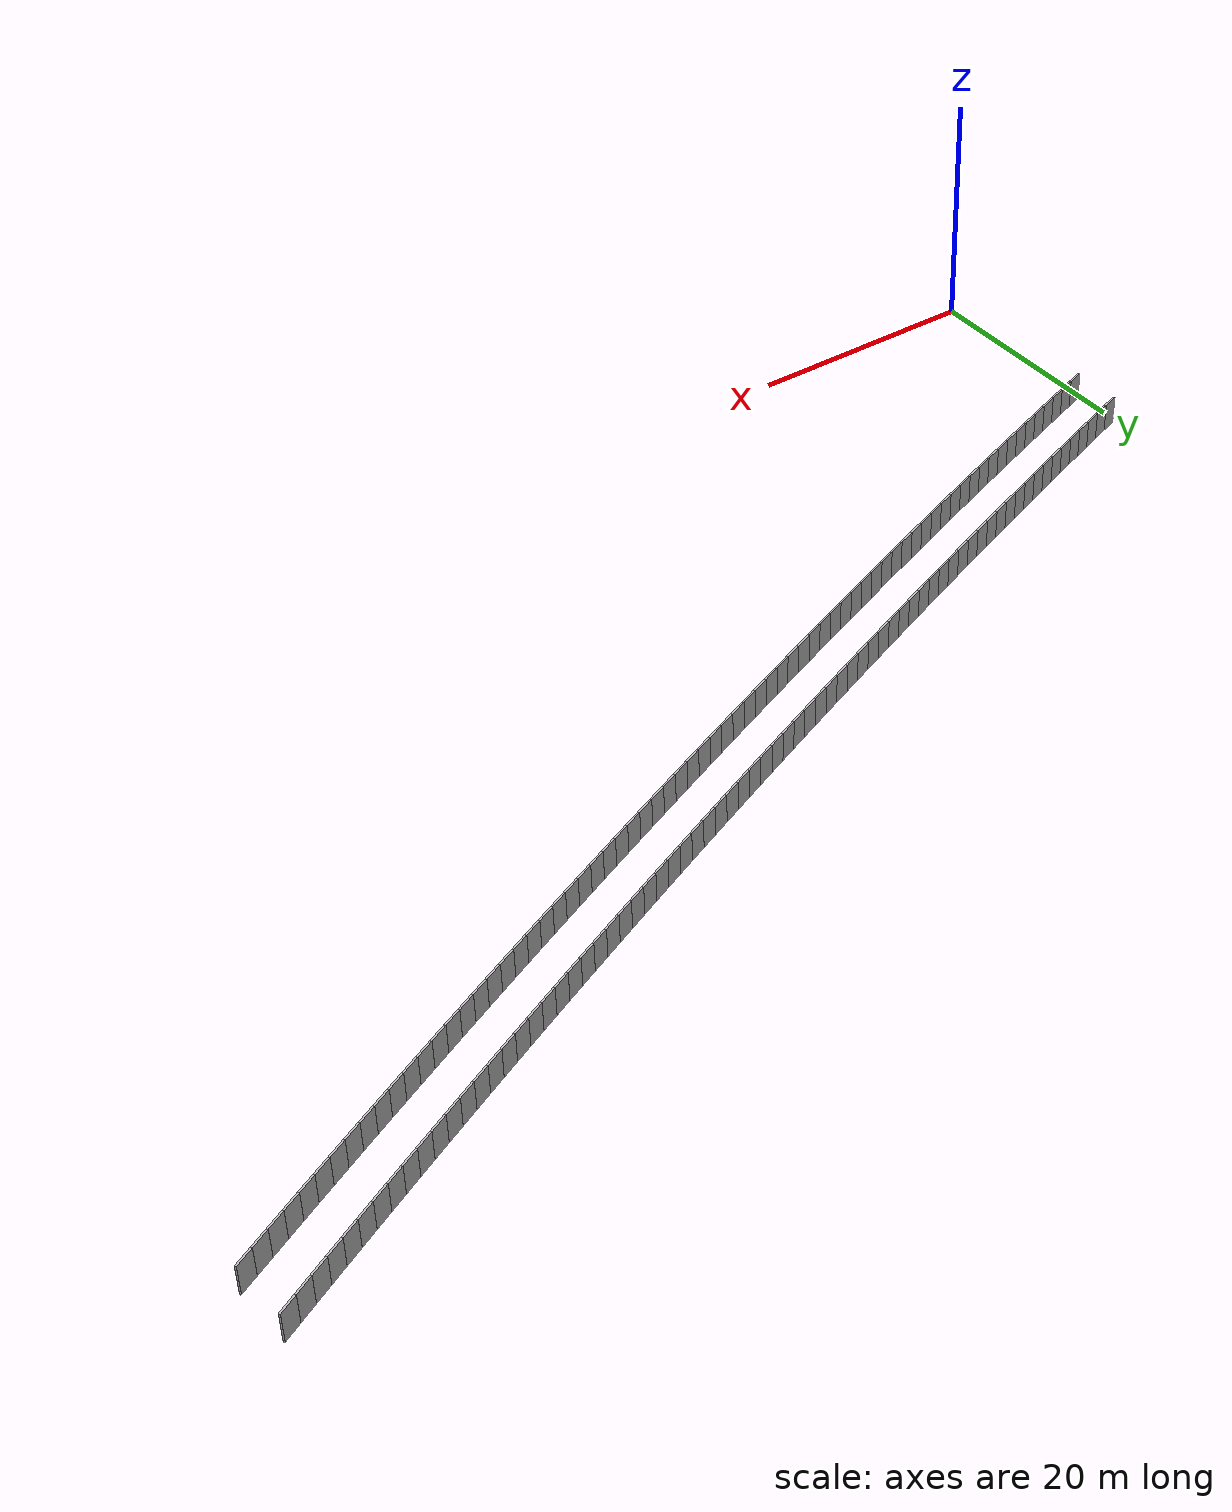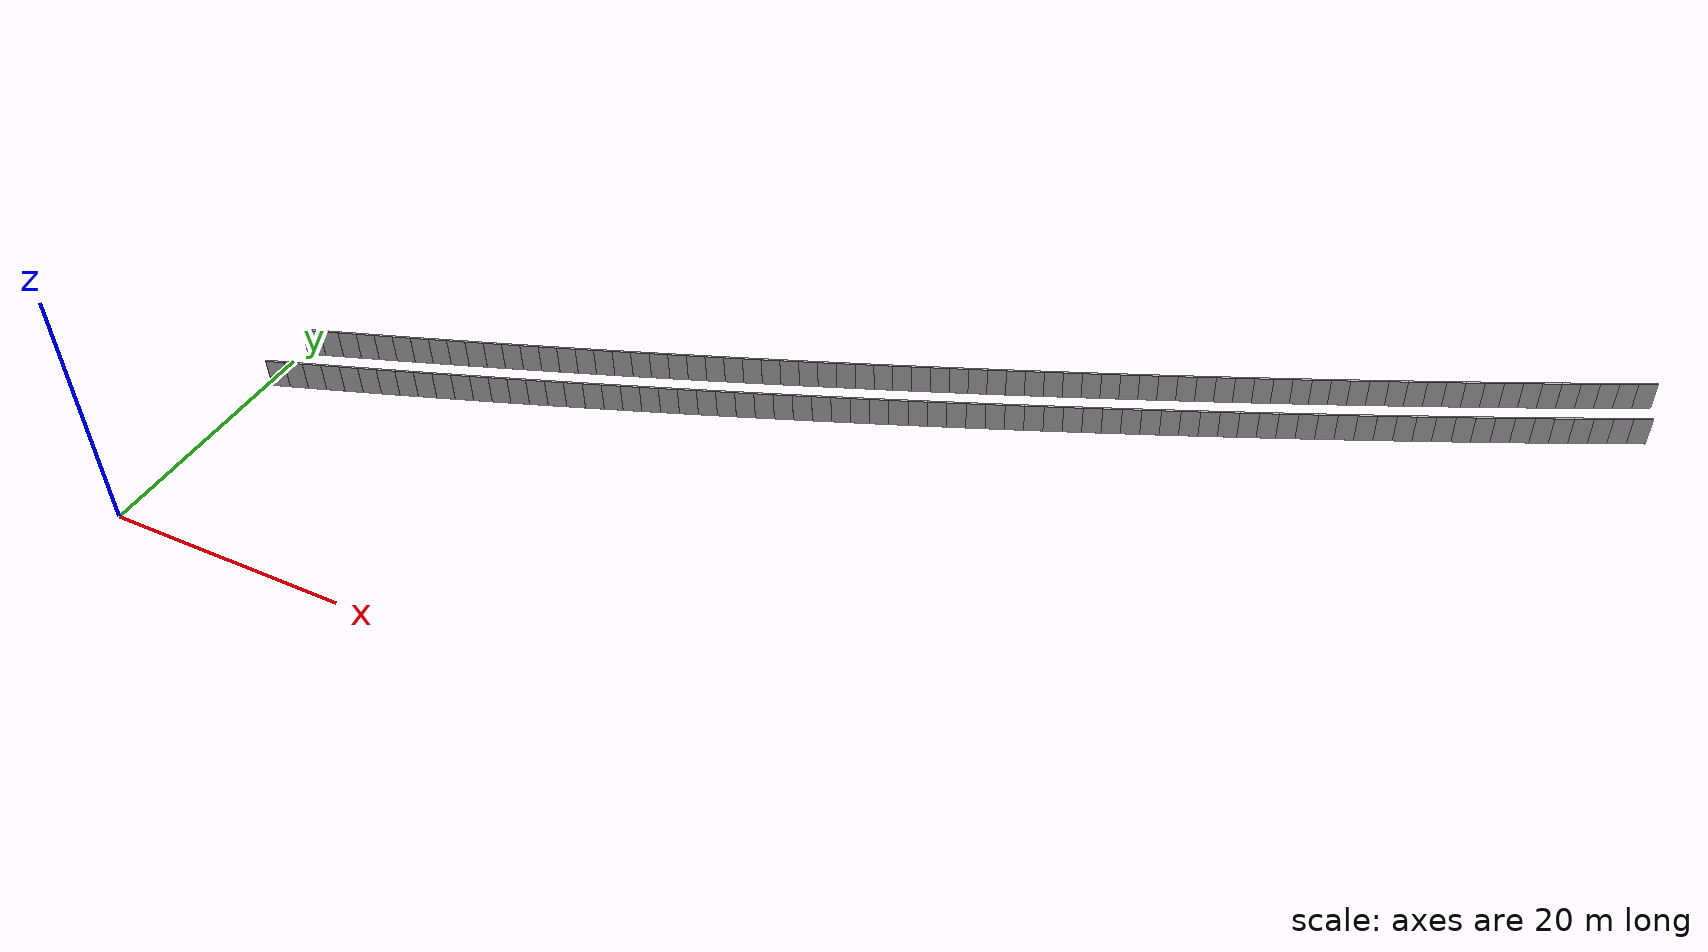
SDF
<?xml version="1.0" ?>
<sdf version="1.6">
  <model name="sps_1602">
    <pose frame="">0 0 0 0 -0 0</pose>
    <static>1</static>
    <self_collide>0</self_collide>
    <allow_auto_disable>0</allow_auto_disable>
    <link name="Wall3916">
      <kinematic>0</kinematic>
      <gravity>1</gravity>
      <self_collide>0</self_collide>
      <collision name="collision">
        <geometry>
          <box>
            <size>1.49652 0.15 2.5</size>
          </box>
        </geometry>
        <pose frame="">0 0 0 0 -0 0</pose>
      </collision>
      <visual name="visual">
        <geometry>
          <box>
            <size>1.49652 0.15 2.5</size>
          </box>
        </geometry>
        <pose frame="">0 0 0 0 -0 0</pose>
        <cast_shadows>1</cast_shadows>
        <transparency>0.0</transparency>
      </visual>
      <pose frame="">1.07986 21.6267 1.25 0 -0 0.335254</pose>
    </link>
    <link name="Wall3917">
      <kinematic>0</kinematic>
      <gravity>1</gravity>
      <self_collide>0</self_collide>
      <collision name="collision">
        <geometry>
          <box>
            <size>1.49661 0.15 2.5</size>
          </box>
        </geometry>
        <pose frame="">0 0 0 0 -0 0</pose>
      </collision>
      <visual name="visual">
        <geometry>
          <box>
            <size>1.49661 0.15 2.5</size>
          </box>
        </geometry>
        <pose frame="">0 0 0 0 -0 0</pose>
        <cast_shadows>1</cast_shadows>
        <transparency>0.0</transparency>
      </visual>
      <pose frame="">2.49276 22.1201 1.25 0 -0 0.336659</pose>
    </link>
    <link name="Wall3918">
      <kinematic>0</kinematic>
      <gravity>1</gravity>
      <self_collide>0</self_collide>
      <collision name="collision">
        <geometry>
          <box>
            <size>1.49656 0.15 2.5</size>
          </box>
        </geometry>
        <pose frame="">0 0 0 0 -0 0</pose>
      </collision>
      <visual name="visual">
        <geometry>
          <box>
            <size>1.49656 0.15 2.5</size>
          </box>
        </geometry>
        <pose frame="">0 0 0 0 -0 0</pose>
        <cast_shadows>1</cast_shadows>
        <transparency>0.0</transparency>
      </visual>
      <pose frame="">3.90487 22.6158 1.25 0 -0 0.33853</pose>
    </link>
    <link name="Wall3919">
      <kinematic>0</kinematic>
      <gravity>1</gravity>
      <self_collide>0</self_collide>
      <collision name="collision">
        <geometry>
          <box>
            <size>1.49636 0.15 2.5</size>
          </box>
        </geometry>
        <pose frame="">0 0 0 0 -0 0</pose>
      </collision>
      <visual name="visual">
        <geometry>
          <box>
            <size>1.49636 0.15 2.5</size>
          </box>
        </geometry>
        <pose frame="">0 0 0 0 -0 0</pose>
        <cast_shadows>1</cast_shadows>
        <transparency>0.0</transparency>
      </visual>
      <pose frame="">5.31606 23.1137 1.25 0 -0 0.339874</pose>
    </link>
    <link name="Wall3920">
      <kinematic>0</kinematic>
      <gravity>1</gravity>
      <self_collide>0</self_collide>
      <collision name="collision">
        <geometry>
          <box>
            <size>1.49645 0.15 2.5</size>
          </box>
        </geometry>
        <pose frame="">0 0 0 0 -0 0</pose>
      </collision>
      <visual name="visual">
        <geometry>
          <box>
            <size>1.49645 0.15 2.5</size>
          </box>
        </geometry>
        <pose frame="">0 0 0 0 -0 0</pose>
        <cast_shadows>1</cast_shadows>
        <transparency>0.0</transparency>
      </visual>
      <pose frame="">6.72646 23.6137 1.25 0 -0 0.341498</pose>
    </link>
    <link name="Wall3921">
      <kinematic>0</kinematic>
      <gravity>1</gravity>
      <self_collide>0</self_collide>
      <collision name="collision">
        <geometry>
          <box>
            <size>1.49664 0.15 2.5</size>
          </box>
        </geometry>
        <pose frame="">0 0 0 0 -0 0</pose>
      </collision>
      <visual name="visual">
        <geometry>
          <box>
            <size>1.49664 0.15 2.5</size>
          </box>
        </geometry>
        <pose frame="">0 0 0 0 -0 0</pose>
        <cast_shadows>1</cast_shadows>
        <transparency>0.0</transparency>
      </visual>
      <pose frame="">8.13616 24.1161 1.25 0 -0 0.343186</pose>
    </link>
    <link name="Wall3922">
      <kinematic>0</kinematic>
      <gravity>1</gravity>
      <self_collide>0</self_collide>
      <collision name="collision">
        <geometry>
          <box>
            <size>1.49646 0.15 2.5</size>
          </box>
        </geometry>
        <pose frame="">0 0 0 0 -0 0</pose>
      </collision>
      <visual name="visual">
        <geometry>
          <box>
            <size>1.49646 0.15 2.5</size>
          </box>
        </geometry>
        <pose frame="">0 0 0 0 -0 0</pose>
        <cast_shadows>1</cast_shadows>
        <transparency>0.0</transparency>
      </visual>
      <pose frame="">9.54504 24.6208 1.25 0 -0 0.344788</pose>
    </link>
    <link name="Wall3923">
      <kinematic>0</kinematic>
      <gravity>1</gravity>
      <self_collide>0</self_collide>
      <collision name="collision">
        <geometry>
          <box>
            <size>1.49651 0.15 2.5</size>
          </box>
        </geometry>
        <pose frame="">0 0 0 0 -0 0</pose>
      </collision>
      <visual name="visual">
        <geometry>
          <box>
            <size>1.49651 0.15 2.5</size>
          </box>
        </geometry>
        <pose frame="">0 0 0 0 -0 0</pose>
        <cast_shadows>1</cast_shadows>
        <transparency>0.0</transparency>
      </visual>
      <pose frame="">10.9531 25.1277 1.25 0 -0 0.346335</pose>
    </link>
    <link name="Wall3924">
      <kinematic>0</kinematic>
      <gravity>1</gravity>
      <self_collide>0</self_collide>
      <collision name="collision">
        <geometry>
          <box>
            <size>1.49671 0.15 2.5</size>
          </box>
        </geometry>
        <pose frame="">0 0 0 0 -0 0</pose>
      </collision>
      <visual name="visual">
        <geometry>
          <box>
            <size>1.49671 0.15 2.5</size>
          </box>
        </geometry>
        <pose frame="">0 0 0 0 -0 0</pose>
        <cast_shadows>1</cast_shadows>
        <transparency>0.0</transparency>
      </visual>
      <pose frame="">12.3604 25.6369 1.25 0 -0 0.348022</pose>
    </link>
    <link name="Wall3925">
      <kinematic>0</kinematic>
      <gravity>1</gravity>
      <self_collide>0</self_collide>
      <collision name="collision">
        <geometry>
          <box>
            <size>1.4964 0.15 2.5</size>
          </box>
        </geometry>
        <pose frame="">0 0 0 0 -0 0</pose>
      </collision>
      <visual name="visual">
        <geometry>
          <box>
            <size>1.4964 0.15 2.5</size>
          </box>
        </geometry>
        <pose frame="">0 0 0 0 -0 0</pose>
        <cast_shadows>1</cast_shadows>
        <transparency>0.0</transparency>
      </visual>
      <pose frame="">13.7669 26.1482 1.25 0 -0 0.349356</pose>
    </link>
    <link name="Wall3926">
      <kinematic>0</kinematic>
      <gravity>1</gravity>
      <self_collide>0</self_collide>
      <collision name="collision">
        <geometry>
          <box>
            <size>1.49647 0.15 2.5</size>
          </box>
        </geometry>
        <pose frame="">0 0 0 0 -0 0</pose>
      </collision>
      <visual name="visual">
        <geometry>
          <box>
            <size>1.49647 0.15 2.5</size>
          </box>
        </geometry>
        <pose frame="">0 0 0 0 -0 0</pose>
        <cast_shadows>1</cast_shadows>
        <transparency>0.0</transparency>
      </visual>
      <pose frame="">15.1725 26.6616 1.25 0 -0 0.351033</pose>
    </link>
    <link name="Wall3927">
      <kinematic>0</kinematic>
      <gravity>1</gravity>
      <self_collide>0</self_collide>
      <collision name="collision">
        <geometry>
          <box>
            <size>1.49649 0.15 2.5</size>
          </box>
        </geometry>
        <pose frame="">0 0 0 0 -0 0</pose>
      </collision>
      <visual name="visual">
        <geometry>
          <box>
            <size>1.49649 0.15 2.5</size>
          </box>
        </geometry>
        <pose frame="">0 0 0 0 -0 0</pose>
        <cast_shadows>1</cast_shadows>
        <transparency>0.0</transparency>
      </visual>
      <pose frame="">16.5773 27.1774 1.25 0 -0 0.352722</pose>
    </link>
    <link name="Wall3928">
      <kinematic>0</kinematic>
      <gravity>1</gravity>
      <self_collide>0</self_collide>
      <collision name="collision">
        <geometry>
          <box>
            <size>1.49652 0.15 2.5</size>
          </box>
        </geometry>
        <pose frame="">0 0 0 0 -0 0</pose>
      </collision>
      <visual name="visual">
        <geometry>
          <box>
            <size>1.49652 0.15 2.5</size>
          </box>
        </geometry>
        <pose frame="">0 0 0 0 -0 0</pose>
        <cast_shadows>1</cast_shadows>
        <transparency>0.0</transparency>
      </visual>
      <pose frame="">17.9813 27.6954 1.25 0 -0 0.354193</pose>
    </link>
    <link name="Wall3929">
      <kinematic>0</kinematic>
      <gravity>1</gravity>
      <self_collide>0</self_collide>
      <collision name="collision">
        <geometry>
          <box>
            <size>1.49652 0.15 2.5</size>
          </box>
        </geometry>
        <pose frame="">0 0 0 0 -0 0</pose>
      </collision>
      <visual name="visual">
        <geometry>
          <box>
            <size>1.49652 0.15 2.5</size>
          </box>
        </geometry>
        <pose frame="">0 0 0 0 -0 0</pose>
        <cast_shadows>1</cast_shadows>
        <transparency>0.0</transparency>
      </visual>
      <pose frame="">19.3845 28.2156 1.25 0 -0 0.355845</pose>
    </link>
    <link name="Wall3930">
      <kinematic>0</kinematic>
      <gravity>1</gravity>
      <self_collide>0</self_collide>
      <collision name="collision">
        <geometry>
          <box>
            <size>1.49663 0.15 2.5</size>
          </box>
        </geometry>
        <pose frame="">0 0 0 0 -0 0</pose>
      </collision>
      <visual name="visual">
        <geometry>
          <box>
            <size>1.49663 0.15 2.5</size>
          </box>
        </geometry>
        <pose frame="">0 0 0 0 -0 0</pose>
        <cast_shadows>1</cast_shadows>
        <transparency>0.0</transparency>
      </visual>
      <pose frame="">20.7869 28.7381 1.25 0 -0 0.357429</pose>
    </link>
    <link name="Wall3931">
      <kinematic>0</kinematic>
      <gravity>1</gravity>
      <self_collide>0</self_collide>
      <collision name="collision">
        <geometry>
          <box>
            <size>1.4966 0.15 2.5</size>
          </box>
        </geometry>
        <pose frame="">0 0 0 0 -0 0</pose>
      </collision>
      <visual name="visual">
        <geometry>
          <box>
            <size>1.4966 0.15 2.5</size>
          </box>
        </geometry>
        <pose frame="">0 0 0 0 -0 0</pose>
        <cast_shadows>1</cast_shadows>
        <transparency>0.0</transparency>
      </visual>
      <pose frame="">22.1885 29.2628 1.25 0 -0 0.359005</pose>
    </link>
    <link name="Wall3932">
      <kinematic>0</kinematic>
      <gravity>1</gravity>
      <self_collide>0</self_collide>
      <collision name="collision">
        <geometry>
          <box>
            <size>1.49661 0.15 2.5</size>
          </box>
        </geometry>
        <pose frame="">0 0 0 0 -0 0</pose>
      </collision>
      <visual name="visual">
        <geometry>
          <box>
            <size>1.49661 0.15 2.5</size>
          </box>
        </geometry>
        <pose frame="">0 0 0 0 -0 0</pose>
        <cast_shadows>1</cast_shadows>
        <transparency>0.0</transparency>
      </visual>
      <pose frame="">23.5893 29.7897 1.25 0 -0 0.360527</pose>
    </link>
    <link name="Wall3933">
      <kinematic>0</kinematic>
      <gravity>1</gravity>
      <self_collide>0</self_collide>
      <collision name="collision">
        <geometry>
          <box>
            <size>1.49649 0.15 2.5</size>
          </box>
        </geometry>
        <pose frame="">0 0 0 0 -0 0</pose>
      </collision>
      <visual name="visual">
        <geometry>
          <box>
            <size>1.49649 0.15 2.5</size>
          </box>
        </geometry>
        <pose frame="">0 0 0 0 -0 0</pose>
        <cast_shadows>1</cast_shadows>
        <transparency>0.0</transparency>
      </visual>
      <pose frame="">24.9892 30.3188 1.25 0 -0 0.362169</pose>
    </link>
    <link name="Wall3934">
      <kinematic>0</kinematic>
      <gravity>1</gravity>
      <self_collide>0</self_collide>
      <collision name="collision">
        <geometry>
          <box>
            <size>1.49653 0.15 2.5</size>
          </box>
        </geometry>
        <pose frame="">0 0 0 0 -0 0</pose>
      </collision>
      <visual name="visual">
        <geometry>
          <box>
            <size>1.49653 0.15 2.5</size>
          </box>
        </geometry>
        <pose frame="">0 0 0 0 -0 0</pose>
        <cast_shadows>1</cast_shadows>
        <transparency>0.0</transparency>
      </visual>
      <pose frame="">26.3882 30.8501 1.25 0 -0 0.36373</pose>
    </link>
    <link name="Wall3935">
      <kinematic>0</kinematic>
      <gravity>1</gravity>
      <self_collide>0</self_collide>
      <collision name="collision">
        <geometry>
          <box>
            <size>1.49658 0.15 2.5</size>
          </box>
        </geometry>
        <pose frame="">0 0 0 0 -0 0</pose>
      </collision>
      <visual name="visual">
        <geometry>
          <box>
            <size>1.49658 0.15 2.5</size>
          </box>
        </geometry>
        <pose frame="">0 0 0 0 -0 0</pose>
        <cast_shadows>1</cast_shadows>
        <transparency>0.0</transparency>
      </visual>
      <pose frame="">27.7864 31.3837 1.25 0 -0 0.36542</pose>
    </link>
    <link name="Wall3936">
      <kinematic>0</kinematic>
      <gravity>1</gravity>
      <self_collide>0</self_collide>
      <collision name="collision">
        <geometry>
          <box>
            <size>1.49639 0.15 2.5</size>
          </box>
        </geometry>
        <pose frame="">0 0 0 0 -0 0</pose>
      </collision>
      <visual name="visual">
        <geometry>
          <box>
            <size>1.49639 0.15 2.5</size>
          </box>
        </geometry>
        <pose frame="">0 0 0 0 -0 0</pose>
        <cast_shadows>1</cast_shadows>
        <transparency>0.0</transparency>
      </visual>
      <pose frame="">29.1836 31.9195 1.25 0 -0 0.36691</pose>
    </link>
    <link name="Wall3937">
      <kinematic>0</kinematic>
      <gravity>1</gravity>
      <self_collide>0</self_collide>
      <collision name="collision">
        <geometry>
          <box>
            <size>1.4965 0.15 2.5</size>
          </box>
        </geometry>
        <pose frame="">0 0 0 0 -0 0</pose>
      </collision>
      <visual name="visual">
        <geometry>
          <box>
            <size>1.4965 0.15 2.5</size>
          </box>
        </geometry>
        <pose frame="">0 0 0 0 -0 0</pose>
        <cast_shadows>1</cast_shadows>
        <transparency>0.0</transparency>
      </visual>
      <pose frame="">30.58 32.4575 1.25 0 -0 0.368585</pose>
    </link>
    <link name="Wall3938">
      <kinematic>0</kinematic>
      <gravity>1</gravity>
      <self_collide>0</self_collide>
      <collision name="collision">
        <geometry>
          <box>
            <size>1.49649 0.15 2.5</size>
          </box>
        </geometry>
        <pose frame="">0 0 0 0 -0 0</pose>
      </collision>
      <visual name="visual">
        <geometry>
          <box>
            <size>1.49649 0.15 2.5</size>
          </box>
        </geometry>
        <pose frame="">0 0 0 0 -0 0</pose>
        <cast_shadows>1</cast_shadows>
        <transparency>0.0</transparency>
      </visual>
      <pose frame="">31.9756 32.9977 1.25 0 -0 0.370032</pose>
    </link>
    <link name="Wall3939">
      <kinematic>0</kinematic>
      <gravity>1</gravity>
      <self_collide>0</self_collide>
      <collision name="collision">
        <geometry>
          <box>
            <size>1.49657 0.15 2.5</size>
          </box>
        </geometry>
        <pose frame="">0 0 0 0 -0 0</pose>
      </collision>
      <visual name="visual">
        <geometry>
          <box>
            <size>1.49657 0.15 2.5</size>
          </box>
        </geometry>
        <pose frame="">0 0 0 0 -0 0</pose>
        <cast_shadows>1</cast_shadows>
        <transparency>0.0</transparency>
      </visual>
      <pose frame="">33.3704 33.54 1.25 0 -0 0.37163</pose>
    </link>
    <link name="Wall3940">
      <kinematic>0</kinematic>
      <gravity>1</gravity>
      <self_collide>0</self_collide>
      <collision name="collision">
        <geometry>
          <box>
            <size>1.49668 0.15 2.5</size>
          </box>
        </geometry>
        <pose frame="">0 0 0 0 -0 0</pose>
      </collision>
      <visual name="visual">
        <geometry>
          <box>
            <size>1.49668 0.15 2.5</size>
          </box>
        </geometry>
        <pose frame="">0 0 0 0 -0 0</pose>
        <cast_shadows>1</cast_shadows>
        <transparency>0.0</transparency>
      </visual>
      <pose frame="">34.7645 34.0846 1.25 0 -0 0.373267</pose>
    </link>
    <link name="Wall3941">
      <kinematic>0</kinematic>
      <gravity>1</gravity>
      <self_collide>0</self_collide>
      <collision name="collision">
        <geometry>
          <box>
            <size>1.49645 0.15 2.5</size>
          </box>
        </geometry>
        <pose frame="">0 0 0 0 -0 0</pose>
      </collision>
      <visual name="visual">
        <geometry>
          <box>
            <size>1.49645 0.15 2.5</size>
          </box>
        </geometry>
        <pose frame="">0 0 0 0 -0 0</pose>
        <cast_shadows>1</cast_shadows>
        <transparency>0.0</transparency>
      </visual>
      <pose frame="">36.1576 34.6314 1.25 0 -0 0.374773</pose>
    </link>
    <link name="Wall3942">
      <kinematic>0</kinematic>
      <gravity>1</gravity>
      <self_collide>0</self_collide>
      <collision name="collision">
        <geometry>
          <box>
            <size>1.49643 0.15 2.5</size>
          </box>
        </geometry>
        <pose frame="">0 0 0 0 -0 0</pose>
      </collision>
      <visual name="visual">
        <geometry>
          <box>
            <size>1.49643 0.15 2.5</size>
          </box>
        </geometry>
        <pose frame="">0 0 0 0 -0 0</pose>
        <cast_shadows>1</cast_shadows>
        <transparency>0.0</transparency>
      </visual>
      <pose frame="">37.5496 35.1804 1.25 0 -0 0.37653</pose>
    </link>
    <link name="Wall3943">
      <kinematic>0</kinematic>
      <gravity>1</gravity>
      <self_collide>0</self_collide>
      <collision name="collision">
        <geometry>
          <box>
            <size>1.49658 0.15 2.5</size>
          </box>
        </geometry>
        <pose frame="">0 0 0 0 -0 0</pose>
      </collision>
      <visual name="visual">
        <geometry>
          <box>
            <size>1.49658 0.15 2.5</size>
          </box>
        </geometry>
        <pose frame="">0 0 0 0 -0 0</pose>
        <cast_shadows>1</cast_shadows>
        <transparency>0.0</transparency>
      </visual>
      <pose frame="">38.9409 35.7316 1.25 0 -0 0.377894</pose>
    </link>
    <link name="Wall3944">
      <kinematic>0</kinematic>
      <gravity>1</gravity>
      <self_collide>0</self_collide>
      <collision name="collision">
        <geometry>
          <box>
            <size>1.49656 0.15 2.5</size>
          </box>
        </geometry>
        <pose frame="">0 0 0 0 -0 0</pose>
      </collision>
      <visual name="visual">
        <geometry>
          <box>
            <size>1.49656 0.15 2.5</size>
          </box>
        </geometry>
        <pose frame="">0 0 0 0 -0 0</pose>
        <cast_shadows>1</cast_shadows>
        <transparency>0.0</transparency>
      </visual>
      <pose frame="">40.3314 36.285 1.25 0 -0 0.379613</pose>
    </link>
    <link name="Wall3945">
      <kinematic>0</kinematic>
      <gravity>1</gravity>
      <self_collide>0</self_collide>
      <collision name="collision">
        <geometry>
          <box>
            <size>1.49666 0.15 2.5</size>
          </box>
        </geometry>
        <pose frame="">0 0 0 0 -0 0</pose>
      </collision>
      <visual name="visual">
        <geometry>
          <box>
            <size>1.49666 0.15 2.5</size>
          </box>
        </geometry>
        <pose frame="">0 0 0 0 -0 0</pose>
        <cast_shadows>1</cast_shadows>
        <transparency>0.0</transparency>
      </visual>
      <pose frame="">41.7211 36.8407 1.25 0 -0 0.381211</pose>
    </link>
    <link name="Wall3946">
      <kinematic>0</kinematic>
      <gravity>1</gravity>
      <self_collide>0</self_collide>
      <collision name="collision">
        <geometry>
          <box>
            <size>1.49642 0.15 2.5</size>
          </box>
        </geometry>
        <pose frame="">0 0 0 0 -0 0</pose>
      </collision>
      <visual name="visual">
        <geometry>
          <box>
            <size>1.49642 0.15 2.5</size>
          </box>
        </geometry>
        <pose frame="">0 0 0 0 -0 0</pose>
        <cast_shadows>1</cast_shadows>
        <transparency>0.0</transparency>
      </visual>
      <pose frame="">43.1098 37.3985 1.25 0 -0 0.38268</pose>
    </link>
    <link name="Wall3947">
      <kinematic>0</kinematic>
      <gravity>1</gravity>
      <self_collide>0</self_collide>
      <collision name="collision">
        <geometry>
          <box>
            <size>1.49636 0.15 2.5</size>
          </box>
        </geometry>
        <pose frame="">0 0 0 0 -0 0</pose>
      </collision>
      <visual name="visual">
        <geometry>
          <box>
            <size>1.49636 0.15 2.5</size>
          </box>
        </geometry>
        <pose frame="">0 0 0 0 -0 0</pose>
        <cast_shadows>1</cast_shadows>
        <transparency>0.0</transparency>
      </visual>
      <pose frame="">44.4975 37.9584 1.25 0 -0 0.384324</pose>
    </link>
    <link name="Wall3948">
      <kinematic>0</kinematic>
      <gravity>1</gravity>
      <self_collide>0</self_collide>
      <collision name="collision">
        <geometry>
          <box>
            <size>1.49643 0.15 2.5</size>
          </box>
        </geometry>
        <pose frame="">0 0 0 0 -0 0</pose>
      </collision>
      <visual name="visual">
        <geometry>
          <box>
            <size>1.49643 0.15 2.5</size>
          </box>
        </geometry>
        <pose frame="">0 0 0 0 -0 0</pose>
        <cast_shadows>1</cast_shadows>
        <transparency>0.0</transparency>
      </visual>
      <pose frame="">45.8843 38.5205 1.25 0 -0 0.385846</pose>
    </link>
    <link name="Wall3949">
      <kinematic>0</kinematic>
      <gravity>1</gravity>
      <self_collide>0</self_collide>
      <collision name="collision">
        <geometry>
          <box>
            <size>1.49679 0.15 2.5</size>
          </box>
        </geometry>
        <pose frame="">0 0 0 0 -0 0</pose>
      </collision>
      <visual name="visual">
        <geometry>
          <box>
            <size>1.49679 0.15 2.5</size>
          </box>
        </geometry>
        <pose frame="">0 0 0 0 -0 0</pose>
        <cast_shadows>1</cast_shadows>
        <transparency>0.0</transparency>
      </visual>
      <pose frame="">47.2704 39.0849 1.25 0 -0 0.387511</pose>
    </link>
    <link name="Wall3950">
      <kinematic>0</kinematic>
      <gravity>1</gravity>
      <self_collide>0</self_collide>
      <collision name="collision">
        <geometry>
          <box>
            <size>1.49649 0.15 2.5</size>
          </box>
        </geometry>
        <pose frame="">0 0 0 0 -0 0</pose>
      </collision>
      <visual name="visual">
        <geometry>
          <box>
            <size>1.49649 0.15 2.5</size>
          </box>
        </geometry>
        <pose frame="">0 0 0 0 -0 0</pose>
        <cast_shadows>1</cast_shadows>
        <transparency>0.0</transparency>
      </visual>
      <pose frame="">48.6556 39.6516 1.25 0 -0 0.389178</pose>
    </link>
    <link name="Wall3951">
      <kinematic>0</kinematic>
      <gravity>1</gravity>
      <self_collide>0</self_collide>
      <collision name="collision">
        <geometry>
          <box>
            <size>1.4965 0.15 2.5</size>
          </box>
        </geometry>
        <pose frame="">0 0 0 0 -0 0</pose>
      </collision>
      <visual name="visual">
        <geometry>
          <box>
            <size>1.4965 0.15 2.5</size>
          </box>
        </geometry>
        <pose frame="">0 0 0 0 -0 0</pose>
        <cast_shadows>1</cast_shadows>
        <transparency>0.0</transparency>
      </visual>
      <pose frame="">50.0398 40.2204 1.25 0 -0 0.390587</pose>
    </link>
    <link name="Wall3952">
      <kinematic>0</kinematic>
      <gravity>1</gravity>
      <self_collide>0</self_collide>
      <collision name="collision">
        <geometry>
          <box>
            <size>1.49653 0.15 2.5</size>
          </box>
        </geometry>
        <pose frame="">0 0 0 0 -0 0</pose>
      </collision>
      <visual name="visual">
        <geometry>
          <box>
            <size>1.49653 0.15 2.5</size>
          </box>
        </geometry>
        <pose frame="">0 0 0 0 -0 0</pose>
        <cast_shadows>1</cast_shadows>
        <transparency>0.0</transparency>
      </visual>
      <pose frame="">51.4231 40.7914 1.25 0 -0 0.392344</pose>
    </link>
    <link name="Wall3953">
      <kinematic>0</kinematic>
      <gravity>1</gravity>
      <self_collide>0</self_collide>
      <collision name="collision">
        <geometry>
          <box>
            <size>1.49641 0.15 2.5</size>
          </box>
        </geometry>
        <pose frame="">0 0 0 0 -0 0</pose>
      </collision>
      <visual name="visual">
        <geometry>
          <box>
            <size>1.49641 0.15 2.5</size>
          </box>
        </geometry>
        <pose frame="">0 0 0 0 -0 0</pose>
        <cast_shadows>1</cast_shadows>
        <transparency>0.0</transparency>
      </visual>
      <pose frame="">52.8054 41.3647 1.25 0 -0 0.393966</pose>
    </link>
    <link name="Wall3954">
      <kinematic>0</kinematic>
      <gravity>1</gravity>
      <self_collide>0</self_collide>
      <collision name="collision">
        <geometry>
          <box>
            <size>1.49658 0.15 2.5</size>
          </box>
        </geometry>
        <pose frame="">0 0 0 0 -0 0</pose>
      </collision>
      <visual name="visual">
        <geometry>
          <box>
            <size>1.49658 0.15 2.5</size>
          </box>
        </geometry>
        <pose frame="">0 0 0 0 -0 0</pose>
        <cast_shadows>1</cast_shadows>
        <transparency>0.0</transparency>
      </visual>
      <pose frame="">54.1868 41.9402 1.25 0 -0 0.39551</pose>
    </link>
    <link name="Wall3955">
      <kinematic>0</kinematic>
      <gravity>1</gravity>
      <self_collide>0</self_collide>
      <collision name="collision">
        <geometry>
          <box>
            <size>1.49657 0.15 2.5</size>
          </box>
        </geometry>
        <pose frame="">0 0 0 0 -0 0</pose>
      </collision>
      <visual name="visual">
        <geometry>
          <box>
            <size>1.49657 0.15 2.5</size>
          </box>
        </geometry>
        <pose frame="">0 0 0 0 -0 0</pose>
        <cast_shadows>1</cast_shadows>
        <transparency>0.0</transparency>
      </visual>
      <pose frame="">55.5674 42.5178 1.25 0 -0 0.396971</pose>
    </link>
    <link name="Wall3956">
      <kinematic>0</kinematic>
      <gravity>1</gravity>
      <self_collide>0</self_collide>
      <collision name="collision">
        <geometry>
          <box>
            <size>1.49652 0.15 2.5</size>
          </box>
        </geometry>
        <pose frame="">0 0 0 0 -0 0</pose>
      </collision>
      <visual name="visual">
        <geometry>
          <box>
            <size>1.49652 0.15 2.5</size>
          </box>
        </geometry>
        <pose frame="">0 0 0 0 -0 0</pose>
        <cast_shadows>1</cast_shadows>
        <transparency>0.0</transparency>
      </visual>
      <pose frame="">56.9471 43.0975 1.25 0 -0 0.398578</pose>
    </link>
    <link name="Wall3957">
      <kinematic>0</kinematic>
      <gravity>1</gravity>
      <self_collide>0</self_collide>
      <collision name="collision">
        <geometry>
          <box>
            <size>1.49651 0.15 2.5</size>
          </box>
        </geometry>
        <pose frame="">0 0 0 0 -0 0</pose>
      </collision>
      <visual name="visual">
        <geometry>
          <box>
            <size>1.49651 0.15 2.5</size>
          </box>
        </geometry>
        <pose frame="">0 0 0 0 -0 0</pose>
        <cast_shadows>1</cast_shadows>
        <transparency>0.0</transparency>
      </visual>
      <pose frame="">58.3259 43.6793 1.25 0 -0 0.40004</pose>
    </link>
    <link name="Wall3958">
      <kinematic>0</kinematic>
      <gravity>1</gravity>
      <self_collide>0</self_collide>
      <collision name="collision">
        <geometry>
          <box>
            <size>1.49637 0.15 2.5</size>
          </box>
        </geometry>
        <pose frame="">0 0 0 0 -0 0</pose>
      </collision>
      <visual name="visual">
        <geometry>
          <box>
            <size>1.49637 0.15 2.5</size>
          </box>
        </geometry>
        <pose frame="">0 0 0 0 -0 0</pose>
        <cast_shadows>1</cast_shadows>
        <transparency>0.0</transparency>
      </visual>
      <pose frame="">59.7036 44.2633 1.25 0 -0 0.401807</pose>
    </link>
    <link name="Wall3959">
      <kinematic>0</kinematic>
      <gravity>1</gravity>
      <self_collide>0</self_collide>
      <collision name="collision">
        <geometry>
          <box>
            <size>1.49671 0.15 2.5</size>
          </box>
        </geometry>
        <pose frame="">0 0 0 0 -0 0</pose>
      </collision>
      <visual name="visual">
        <geometry>
          <box>
            <size>1.49671 0.15 2.5</size>
          </box>
        </geometry>
        <pose frame="">0 0 0 0 -0 0</pose>
        <cast_shadows>1</cast_shadows>
        <transparency>0.0</transparency>
      </visual>
      <pose frame="">61.0806 44.8496 1.25 0 -0 0.403264</pose>
    </link>
    <link name="Wall3960">
      <kinematic>0</kinematic>
      <gravity>1</gravity>
      <self_collide>0</self_collide>
      <collision name="collision">
        <geometry>
          <box>
            <size>1.49658 0.15 2.5</size>
          </box>
        </geometry>
        <pose frame="">0 0 0 0 -0 0</pose>
      </collision>
      <visual name="visual">
        <geometry>
          <box>
            <size>1.49658 0.15 2.5</size>
          </box>
        </geometry>
        <pose frame="">0 0 0 0 -0 0</pose>
        <cast_shadows>1</cast_shadows>
        <transparency>0.0</transparency>
      </visual>
      <pose frame="">62.4567 45.4381 1.25 0 -0 0.40494</pose>
    </link>
    <link name="Wall3961">
      <kinematic>0</kinematic>
      <gravity>1</gravity>
      <self_collide>0</self_collide>
      <collision name="collision">
        <geometry>
          <box>
            <size>1.49647 0.15 2.5</size>
          </box>
        </geometry>
        <pose frame="">0 0 0 0 -0 0</pose>
      </collision>
      <visual name="visual">
        <geometry>
          <box>
            <size>1.49647 0.15 2.5</size>
          </box>
        </geometry>
        <pose frame="">0 0 0 0 -0 0</pose>
        <cast_shadows>1</cast_shadows>
        <transparency>0.0</transparency>
      </visual>
      <pose frame="">63.8317 46.0288 1.25 0 -0 0.406616</pose>
    </link>
    <link name="Wall3962">
      <kinematic>0</kinematic>
      <gravity>1</gravity>
      <self_collide>0</self_collide>
      <collision name="collision">
        <geometry>
          <box>
            <size>1.49653 0.15 2.5</size>
          </box>
        </geometry>
        <pose frame="">0 0 0 0 -0 0</pose>
      </collision>
      <visual name="visual">
        <geometry>
          <box>
            <size>1.49653 0.15 2.5</size>
          </box>
        </geometry>
        <pose frame="">0 0 0 0 -0 0</pose>
        <cast_shadows>1</cast_shadows>
        <transparency>0.0</transparency>
      </visual>
      <pose frame="">65.2057 46.6217 1.25 0 -0 0.408153</pose>
    </link>
    <link name="Wall3963">
      <kinematic>0</kinematic>
      <gravity>1</gravity>
      <self_collide>0</self_collide>
      <collision name="collision">
        <geometry>
          <box>
            <size>1.49635 0.15 2.5</size>
          </box>
        </geometry>
        <pose frame="">0 0 0 0 -0 0</pose>
      </collision>
      <visual name="visual">
        <geometry>
          <box>
            <size>1.49635 0.15 2.5</size>
          </box>
        </geometry>
        <pose frame="">0 0 0 0 -0 0</pose>
        <cast_shadows>1</cast_shadows>
        <transparency>0.0</transparency>
      </visual>
      <pose frame="">66.5788 47.2167 1.25 0 -0 0.409626</pose>
    </link>
    <link name="Wall3964">
      <kinematic>0</kinematic>
      <gravity>1</gravity>
      <self_collide>0</self_collide>
      <collision name="collision">
        <geometry>
          <box>
            <size>1.49668 0.15 2.5</size>
          </box>
        </geometry>
        <pose frame="">0 0 0 0 -0 0</pose>
      </collision>
      <visual name="visual">
        <geometry>
          <box>
            <size>1.49668 0.15 2.5</size>
          </box>
        </geometry>
        <pose frame="">0 0 0 0 -0 0</pose>
        <cast_shadows>1</cast_shadows>
        <transparency>0.0</transparency>
      </visual>
      <pose frame="">67.9509 47.8139 1.25 0 -0 0.411355</pose>
    </link>
    <link name="Wall3965">
      <kinematic>0</kinematic>
      <gravity>1</gravity>
      <self_collide>0</self_collide>
      <collision name="collision">
        <geometry>
          <box>
            <size>1.49668 0.15 2.5</size>
          </box>
        </geometry>
        <pose frame="">0 0 0 0 -0 0</pose>
      </collision>
      <visual name="visual">
        <geometry>
          <box>
            <size>1.49668 0.15 2.5</size>
          </box>
        </geometry>
        <pose frame="">0 0 0 0 -0 0</pose>
        <cast_shadows>1</cast_shadows>
        <transparency>0.0</transparency>
      </visual>
      <pose frame="">69.3223 48.4133 1.25 0 -0 0.412779</pose>
    </link>
    <link name="Wall3966">
      <kinematic>0</kinematic>
      <gravity>1</gravity>
      <self_collide>0</self_collide>
      <collision name="collision">
        <geometry>
          <box>
            <size>1.4965 0.15 2.5</size>
          </box>
        </geometry>
        <pose frame="">0 0 0 0 -0 0</pose>
      </collision>
      <visual name="visual">
        <geometry>
          <box>
            <size>1.4965 0.15 2.5</size>
          </box>
        </geometry>
        <pose frame="">0 0 0 0 -0 0</pose>
        <cast_shadows>1</cast_shadows>
        <transparency>0.0</transparency>
      </visual>
      <pose frame="">70.6927 49.0148 1.25 0 -0 0.414435</pose>
    </link>
    <link name="Wall3967">
      <kinematic>0</kinematic>
      <gravity>1</gravity>
      <self_collide>0</self_collide>
      <collision name="collision">
        <geometry>
          <box>
            <size>1.49649 0.15 2.5</size>
          </box>
        </geometry>
        <pose frame="">0 0 0 0 -0 0</pose>
      </collision>
      <visual name="visual">
        <geometry>
          <box>
            <size>1.49649 0.15 2.5</size>
          </box>
        </geometry>
        <pose frame="">0 0 0 0 -0 0</pose>
        <cast_shadows>1</cast_shadows>
        <transparency>0.0</transparency>
      </visual>
      <pose frame="">72.0621 49.6185 1.25 0 -0 0.416042</pose>
    </link>
    <link name="Wall3968">
      <kinematic>0</kinematic>
      <gravity>1</gravity>
      <self_collide>0</self_collide>
      <collision name="collision">
        <geometry>
          <box>
            <size>1.4966 0.15 2.5</size>
          </box>
        </geometry>
        <pose frame="">0 0 0 0 -0 0</pose>
      </collision>
      <visual name="visual">
        <geometry>
          <box>
            <size>1.4966 0.15 2.5</size>
          </box>
        </geometry>
        <pose frame="">0 0 0 0 -0 0</pose>
        <cast_shadows>1</cast_shadows>
        <transparency>0.0</transparency>
      </visual>
      <pose frame="">73.4305 50.2244 1.25 0 -0 0.417616</pose>
    </link>
    <link name="Wall3969">
      <kinematic>0</kinematic>
      <gravity>1</gravity>
      <self_collide>0</self_collide>
      <collision name="collision">
        <geometry>
          <box>
            <size>1.49643 0.15 2.5</size>
          </box>
        </geometry>
        <pose frame="">0 0 0 0 -0 0</pose>
      </collision>
      <visual name="visual">
        <geometry>
          <box>
            <size>1.49643 0.15 2.5</size>
          </box>
        </geometry>
        <pose frame="">0 0 0 0 -0 0</pose>
        <cast_shadows>1</cast_shadows>
        <transparency>0.0</transparency>
      </visual>
      <pose frame="">74.7979 50.8325 1.25 0 -0 0.419272</pose>
    </link>
    <link name="Wall3970">
      <kinematic>0</kinematic>
      <gravity>1</gravity>
      <self_collide>0</self_collide>
      <collision name="collision">
        <geometry>
          <box>
            <size>1.49664 0.15 2.5</size>
          </box>
        </geometry>
        <pose frame="">0 0 0 0 -0 0</pose>
      </collision>
      <visual name="visual">
        <geometry>
          <box>
            <size>1.49664 0.15 2.5</size>
          </box>
        </geometry>
        <pose frame="">0 0 0 0 -0 0</pose>
        <cast_shadows>1</cast_shadows>
        <transparency>0.0</transparency>
      </visual>
      <pose frame="">76.1644 51.4427 1.25 0 -0 0.420684</pose>
    </link>
    <link name="Wall3971">
      <kinematic>0</kinematic>
      <gravity>1</gravity>
      <self_collide>0</self_collide>
      <collision name="collision">
        <geometry>
          <box>
            <size>1.49654 0.15 2.5</size>
          </box>
        </geometry>
        <pose frame="">0 0 0 0 -0 0</pose>
      </collision>
      <visual name="visual">
        <geometry>
          <box>
            <size>1.49654 0.15 2.5</size>
          </box>
        </geometry>
        <pose frame="">0 0 0 0 -0 0</pose>
        <cast_shadows>1</cast_shadows>
        <transparency>0.0</transparency>
      </visual>
      <pose frame="">77.53 52.055 1.25 0 -0 0.422324</pose>
    </link>
    <link name="Wall3972">
      <kinematic>0</kinematic>
      <gravity>1</gravity>
      <self_collide>0</self_collide>
      <collision name="collision">
        <geometry>
          <box>
            <size>1.49651 0.15 2.5</size>
          </box>
        </geometry>
        <pose frame="">0 0 0 0 -0 0</pose>
      </collision>
      <visual name="visual">
        <geometry>
          <box>
            <size>1.49651 0.15 2.5</size>
          </box>
        </geometry>
        <pose frame="">0 0 0 0 -0 0</pose>
        <cast_shadows>1</cast_shadows>
        <transparency>0.0</transparency>
      </visual>
      <pose frame="">78.8945 52.6696 1.25 0 -0 0.424076</pose>
    </link>
    <link name="Wall3973">
      <kinematic>0</kinematic>
      <gravity>1</gravity>
      <self_collide>0</self_collide>
      <collision name="collision">
        <geometry>
          <box>
            <size>1.49651 0.15 2.5</size>
          </box>
        </geometry>
        <pose frame="">0 0 0 0 -0 0</pose>
      </collision>
      <visual name="visual">
        <geometry>
          <box>
            <size>1.49651 0.15 2.5</size>
          </box>
        </geometry>
        <pose frame="">0 0 0 0 -0 0</pose>
        <cast_shadows>1</cast_shadows>
        <transparency>0.0</transparency>
      </visual>
      <pose frame="">80.258 53.2864 1.25 0 -0 0.425554</pose>
    </link>
    <link name="Wall3974">
      <kinematic>0</kinematic>
      <gravity>1</gravity>
      <self_collide>0</self_collide>
      <collision name="collision">
        <geometry>
          <box>
            <size>1.49664 0.15 2.5</size>
          </box>
        </geometry>
        <pose frame="">0 0 0 0 -0 0</pose>
      </collision>
      <visual name="visual">
        <geometry>
          <box>
            <size>1.49664 0.15 2.5</size>
          </box>
        </geometry>
        <pose frame="">0 0 0 0 -0 0</pose>
        <cast_shadows>1</cast_shadows>
        <transparency>0.0</transparency>
      </visual>
      <pose frame="">81.6206 53.9053 1.25 0 -0 0.427127</pose>
    </link>
    <link name="Wall3975">
      <kinematic>0</kinematic>
      <gravity>1</gravity>
      <self_collide>0</self_collide>
      <collision name="collision">
        <geometry>
          <box>
            <size>1.49642 0.15 2.5</size>
          </box>
        </geometry>
        <pose frame="">0 0 0 0 -0 0</pose>
      </collision>
      <visual name="visual">
        <geometry>
          <box>
            <size>1.49642 0.15 2.5</size>
          </box>
        </geometry>
        <pose frame="">0 0 0 0 -0 0</pose>
        <cast_shadows>1</cast_shadows>
        <transparency>0.0</transparency>
      </visual>
      <pose frame="">82.9822 54.5263 1.25 0 -0 0.428673</pose>
    </link>
    <link name="Wall3976">
      <kinematic>0</kinematic>
      <gravity>1</gravity>
      <self_collide>0</self_collide>
      <collision name="collision">
        <geometry>
          <box>
            <size>1.49664 0.15 2.5</size>
          </box>
        </geometry>
        <pose frame="">0 0 0 0 -0 0</pose>
      </collision>
      <visual name="visual">
        <geometry>
          <box>
            <size>1.49664 0.15 2.5</size>
          </box>
        </geometry>
        <pose frame="">0 0 0 0 -0 0</pose>
        <cast_shadows>1</cast_shadows>
        <transparency>0.0</transparency>
      </visual>
      <pose frame="">84.3428 55.1495 1.25 0 -0 0.430357</pose>
    </link>
    <link name="Wall3977">
      <kinematic>0</kinematic>
      <gravity>1</gravity>
      <self_collide>0</self_collide>
      <collision name="collision">
        <geometry>
          <box>
            <size>1.49642 0.15 2.5</size>
          </box>
        </geometry>
        <pose frame="">0 0 0 0 -0 0</pose>
      </collision>
      <visual name="visual">
        <geometry>
          <box>
            <size>1.49642 0.15 2.5</size>
          </box>
        </geometry>
        <pose frame="">0 0 0 0 -0 0</pose>
        <cast_shadows>1</cast_shadows>
        <transparency>0.0</transparency>
      </visual>
      <pose frame="">85.7024 55.7749 1.25 0 -0 0.431904</pose>
    </link>
    <link name="Wall3978">
      <kinematic>0</kinematic>
      <gravity>1</gravity>
      <self_collide>0</self_collide>
      <collision name="collision">
        <geometry>
          <box>
            <size>1.4964 0.15 2.5</size>
          </box>
        </geometry>
        <pose frame="">0 0 0 0 -0 0</pose>
      </collision>
      <visual name="visual">
        <geometry>
          <box>
            <size>1.4964 0.15 2.5</size>
          </box>
        </geometry>
        <pose frame="">0 0 0 0 -0 0</pose>
        <cast_shadows>1</cast_shadows>
        <transparency>0.0</transparency>
      </visual>
      <pose frame="">87.0608 56.4024 1.25 0 -0 0.433527</pose>
    </link>
    <link name="Wall3979">
      <kinematic>0</kinematic>
      <gravity>1</gravity>
      <self_collide>0</self_collide>
      <collision name="collision">
        <geometry>
          <box>
            <size>1.49659 0.15 2.5</size>
          </box>
        </geometry>
        <pose frame="">0 0 0 0 -0 0</pose>
      </collision>
      <visual name="visual">
        <geometry>
          <box>
            <size>1.49659 0.15 2.5</size>
          </box>
        </geometry>
        <pose frame="">0 0 0 0 -0 0</pose>
        <cast_shadows>1</cast_shadows>
        <transparency>0.0</transparency>
      </visual>
      <pose frame="">88.4184 57.032 1.25 0 -0 0.434954</pose>
    </link>
    <link name="Wall3980">
      <kinematic>0</kinematic>
      <gravity>1</gravity>
      <self_collide>0</self_collide>
      <collision name="collision">
        <geometry>
          <box>
            <size>1.49657 0.15 2.5</size>
          </box>
        </geometry>
        <pose frame="">0 0 0 0 -0 0</pose>
      </collision>
      <visual name="visual">
        <geometry>
          <box>
            <size>1.49657 0.15 2.5</size>
          </box>
        </geometry>
        <pose frame="">0 0 0 0 -0 0</pose>
        <cast_shadows>1</cast_shadows>
        <transparency>0.0</transparency>
      </visual>
      <pose frame="">89.7752 57.6637 1.25 0 -0 0.436578</pose>
    </link>
    <link name="Wall3981">
      <kinematic>0</kinematic>
      <gravity>1</gravity>
      <self_collide>0</self_collide>
      <collision name="collision">
        <geometry>
          <box>
            <size>1.49654 0.15 2.5</size>
          </box>
        </geometry>
        <pose frame="">0 0 0 0 -0 0</pose>
      </collision>
      <visual name="visual">
        <geometry>
          <box>
            <size>1.49654 0.15 2.5</size>
          </box>
        </geometry>
        <pose frame="">0 0 0 0 -0 0</pose>
        <cast_shadows>1</cast_shadows>
        <transparency>0.0</transparency>
      </visual>
      <pose frame="">91.1309 58.2976 1.25 0 -0 0.438165</pose>
    </link>
    <link name="Wall3982">
      <kinematic>0</kinematic>
      <gravity>1</gravity>
      <self_collide>0</self_collide>
      <collision name="collision">
        <geometry>
          <box>
            <size>1.49645 0.15 2.5</size>
          </box>
        </geometry>
        <pose frame="">0 0 0 0 -0 0</pose>
      </collision>
      <visual name="visual">
        <geometry>
          <box>
            <size>1.49645 0.15 2.5</size>
          </box>
        </geometry>
        <pose frame="">0 0 0 0 -0 0</pose>
        <cast_shadows>1</cast_shadows>
        <transparency>0.0</transparency>
      </visual>
      <pose frame="">92.4854 58.9337 1.25 0 -0 0.43986</pose>
    </link>
    <link name="Wall3983">
      <kinematic>0</kinematic>
      <gravity>1</gravity>
      <self_collide>0</self_collide>
      <collision name="collision">
        <geometry>
          <box>
            <size>1.49659 0.15 2.5</size>
          </box>
        </geometry>
        <pose frame="">0 0 0 0 -0 0</pose>
      </collision>
      <visual name="visual">
        <geometry>
          <box>
            <size>1.49659 0.15 2.5</size>
          </box>
        </geometry>
        <pose frame="">0 0 0 0 -0 0</pose>
        <cast_shadows>1</cast_shadows>
        <transparency>0.0</transparency>
      </visual>
      <pose frame="">93.839 59.5719 1.25 0 -0 0.441303</pose>
    </link>
    <link name="Wall3984">
      <kinematic>0</kinematic>
      <gravity>1</gravity>
      <self_collide>0</self_collide>
      <collision name="collision">
        <geometry>
          <box>
            <size>1.49643 0.15 2.5</size>
          </box>
        </geometry>
        <pose frame="">0 0 0 0 -0 0</pose>
      </collision>
      <visual name="visual">
        <geometry>
          <box>
            <size>1.49643 0.15 2.5</size>
          </box>
        </geometry>
        <pose frame="">0 0 0 0 -0 0</pose>
        <cast_shadows>1</cast_shadows>
        <transparency>0.0</transparency>
      </visual>
      <pose frame="">95.1916 60.2122 1.25 0 -0 0.44298</pose>
    </link>
    <link name="Wall3985">
      <kinematic>0</kinematic>
      <gravity>1</gravity>
      <self_collide>0</self_collide>
      <collision name="collision">
        <geometry>
          <box>
            <size>1.49663 0.15 2.5</size>
          </box>
        </geometry>
        <pose frame="">0 0 0 0 -0 0</pose>
      </collision>
      <visual name="visual">
        <geometry>
          <box>
            <size>1.49663 0.15 2.5</size>
          </box>
        </geometry>
        <pose frame="">0 0 0 0 -0 0</pose>
        <cast_shadows>1</cast_shadows>
        <transparency>0.0</transparency>
      </visual>
      <pose frame="">96.5432 60.8547 1.25 0 -0 0.444496</pose>
    </link>
    <link name="Wall3986">
      <kinematic>0</kinematic>
      <gravity>1</gravity>
      <self_collide>0</self_collide>
      <collision name="collision">
        <geometry>
          <box>
            <size>1.49655 0.15 2.5</size>
          </box>
        </geometry>
        <pose frame="">0 0 0 0 -0 0</pose>
      </collision>
      <visual name="visual">
        <geometry>
          <box>
            <size>1.49655 0.15 2.5</size>
          </box>
        </geometry>
        <pose frame="">0 0 0 0 -0 0</pose>
        <cast_shadows>1</cast_shadows>
        <transparency>0.0</transparency>
      </visual>
      <pose frame="">97.8939 61.4994 1.25 0 -0 0.446192</pose>
    </link>
    <link name="Wall3987">
      <kinematic>0</kinematic>
      <gravity>1</gravity>
      <self_collide>0</self_collide>
      <collision name="collision">
        <geometry>
          <box>
            <size>1.49657 0.15 2.5</size>
          </box>
        </geometry>
        <pose frame="">0 0 0 0 -0 0</pose>
      </collision>
      <visual name="visual">
        <geometry>
          <box>
            <size>1.49657 0.15 2.5</size>
          </box>
        </geometry>
        <pose frame="">0 0 0 0 -0 0</pose>
        <cast_shadows>1</cast_shadows>
        <transparency>0.0</transparency>
      </visual>
      <pose frame="">99.2434 62.1463 1.25 0 -0 0.447816</pose>
    </link>
    <link name="Wall7690">
      <kinematic>0</kinematic>
      <gravity>1</gravity>
      <self_collide>0</self_collide>
      <collision name="collision">
        <geometry>
          <box>
            <size>1.50309 0.15 2.5</size>
          </box>
        </geometry>
        <pose frame="">0 0 0 0 -0 0</pose>
      </collision>
      <visual name="visual">
        <geometry>
          <box>
            <size>1.50309 0.15 2.5</size>
          </box>
        </geometry>
        <pose frame="">0 0 0 0 -0 0</pose>
        <cast_shadows>1</cast_shadows>
        <transparency>0.0</transparency>
      </visual>
      <pose frame="">1.02434 17.224 1.25 0 -0 0.333603</pose>
    </link>
    <link name="Wall7691">
      <kinematic>0</kinematic>
      <gravity>1</gravity>
      <self_collide>0</self_collide>
      <collision name="collision">
        <geometry>
          <box>
            <size>1.50307 0.15 2.5</size>
          </box>
        </geometry>
        <pose frame="">0 0 0 0 -0 0</pose>
      </collision>
      <visual name="visual">
        <geometry>
          <box>
            <size>1.50307 0.15 2.5</size>
          </box>
        </geometry>
        <pose frame="">0 0 0 0 -0 0</pose>
        <cast_shadows>1</cast_shadows>
        <transparency>0.0</transparency>
      </visual>
      <pose frame="">2.44414 17.7174 1.25 0 -0 0.335285</pose>
    </link>
    <link name="Wall7692">
      <kinematic>0</kinematic>
      <gravity>1</gravity>
      <self_collide>0</self_collide>
      <collision name="collision">
        <geometry>
          <box>
            <size>1.50312 0.15 2.5</size>
          </box>
        </geometry>
        <pose frame="">0 0 0 0 -0 0</pose>
      </collision>
      <visual name="visual">
        <geometry>
          <box>
            <size>1.50312 0.15 2.5</size>
          </box>
        </geometry>
        <pose frame="">0 0 0 0 -0 0</pose>
        <cast_shadows>1</cast_shadows>
        <transparency>0.0</transparency>
      </visual>
      <pose frame="">3.86315 18.2131 1.25 0 -0 0.336865</pose>
    </link>
    <link name="Wall7693">
      <kinematic>0</kinematic>
      <gravity>1</gravity>
      <self_collide>0</self_collide>
      <collision name="collision">
        <geometry>
          <box>
            <size>1.5032 0.15 2.5</size>
          </box>
        </geometry>
        <pose frame="">0 0 0 0 -0 0</pose>
      </collision>
      <visual name="visual">
        <geometry>
          <box>
            <size>1.5032 0.15 2.5</size>
          </box>
        </geometry>
        <pose frame="">0 0 0 0 -0 0</pose>
        <cast_shadows>1</cast_shadows>
        <transparency>0.0</transparency>
      </visual>
      <pose frame="">5.28146 18.711 1.25 0 -0 0.338353</pose>
    </link>
    <link name="Wall7694">
      <kinematic>0</kinematic>
      <gravity>1</gravity>
      <self_collide>0</self_collide>
      <collision name="collision">
        <geometry>
          <box>
            <size>1.50303 0.15 2.5</size>
          </box>
        </geometry>
        <pose frame="">0 0 0 0 -0 0</pose>
      </collision>
      <visual name="visual">
        <geometry>
          <box>
            <size>1.50303 0.15 2.5</size>
          </box>
        </geometry>
        <pose frame="">0 0 0 0 -0 0</pose>
        <cast_shadows>1</cast_shadows>
        <transparency>0.0</transparency>
      </visual>
      <pose frame="">6.69894 19.2111 1.25 0 -0 0.339986</pose>
    </link>
    <link name="Wall7695">
      <kinematic>0</kinematic>
      <gravity>1</gravity>
      <self_collide>0</self_collide>
      <collision name="collision">
        <geometry>
          <box>
            <size>1.50301 0.15 2.5</size>
          </box>
        </geometry>
        <pose frame="">0 0 0 0 -0 0</pose>
      </collision>
      <visual name="visual">
        <geometry>
          <box>
            <size>1.50301 0.15 2.5</size>
          </box>
        </geometry>
        <pose frame="">0 0 0 0 -0 0</pose>
        <cast_shadows>1</cast_shadows>
        <transparency>0.0</transparency>
      </visual>
      <pose frame="">8.11553 19.7134 1.25 0 -0 0.341541</pose>
    </link>
    <link name="Wall7696">
      <kinematic>0</kinematic>
      <gravity>1</gravity>
      <self_collide>0</self_collide>
      <collision name="collision">
        <geometry>
          <box>
            <size>1.50329 0.15 2.5</size>
          </box>
        </geometry>
        <pose frame="">0 0 0 0 -0 0</pose>
      </collision>
      <visual name="visual">
        <geometry>
          <box>
            <size>1.50329 0.15 2.5</size>
          </box>
        </geometry>
        <pose frame="">0 0 0 0 -0 0</pose>
        <cast_shadows>1</cast_shadows>
        <transparency>0.0</transparency>
      </visual>
      <pose frame="">9.53146 20.218 1.25 0 -0 0.343155</pose>
    </link>
    <link name="Wall7697">
      <kinematic>0</kinematic>
      <gravity>1</gravity>
      <self_collide>0</self_collide>
      <collision name="collision">
        <geometry>
          <box>
            <size>1.503 0.15 2.5</size>
          </box>
        </geometry>
        <pose frame="">0 0 0 0 -0 0</pose>
      </collision>
      <visual name="visual">
        <geometry>
          <box>
            <size>1.503 0.15 2.5</size>
          </box>
        </geometry>
        <pose frame="">0 0 0 0 -0 0</pose>
        <cast_shadows>1</cast_shadows>
        <transparency>0.0</transparency>
      </visual>
      <pose frame="">10.9466 20.7249 1.25 0 -0 0.344778</pose>
    </link>
    <link name="Wall7698">
      <kinematic>0</kinematic>
      <gravity>1</gravity>
      <self_collide>0</self_collide>
      <collision name="collision">
        <geometry>
          <box>
            <size>1.50306 0.15 2.5</size>
          </box>
        </geometry>
        <pose frame="">0 0 0 0 -0 0</pose>
      </collision>
      <visual name="visual">
        <geometry>
          <box>
            <size>1.50306 0.15 2.5</size>
          </box>
        </geometry>
        <pose frame="">0 0 0 0 -0 0</pose>
        <cast_shadows>1</cast_shadows>
        <transparency>0.0</transparency>
      </visual>
      <pose frame="">12.3607 21.234 1.25 0 -0 0.346318</pose>
    </link>
    <link name="Wall7699">
      <kinematic>0</kinematic>
      <gravity>1</gravity>
      <self_collide>0</self_collide>
      <collision name="collision">
        <geometry>
          <box>
            <size>1.50306 0.15 2.5</size>
          </box>
        </geometry>
        <pose frame="">0 0 0 0 -0 0</pose>
      </collision>
      <visual name="visual">
        <geometry>
          <box>
            <size>1.50306 0.15 2.5</size>
          </box>
        </geometry>
        <pose frame="">0 0 0 0 -0 0</pose>
        <cast_shadows>1</cast_shadows>
        <transparency>0.0</transparency>
      </visual>
      <pose frame="">13.7742 21.7453 1.25 0 -0 0.347872</pose>
    </link>
    <link name="Wall7700">
      <kinematic>0</kinematic>
      <gravity>1</gravity>
      <self_collide>0</self_collide>
      <collision name="collision">
        <geometry>
          <box>
            <size>1.50301 0.15 2.5</size>
          </box>
        </geometry>
        <pose frame="">0 0 0 0 -0 0</pose>
      </collision>
      <visual name="visual">
        <geometry>
          <box>
            <size>1.50301 0.15 2.5</size>
          </box>
        </geometry>
        <pose frame="">0 0 0 0 -0 0</pose>
        <cast_shadows>1</cast_shadows>
        <transparency>0.0</transparency>
      </visual>
      <pose frame="">15.1868 22.2588 1.25 0 -0 0.349441</pose>
    </link>
    <link name="Wall7701">
      <kinematic>0</kinematic>
      <gravity>1</gravity>
      <self_collide>0</self_collide>
      <collision name="collision">
        <geometry>
          <box>
            <size>1.50316 0.15 2.5</size>
          </box>
        </geometry>
        <pose frame="">0 0 0 0 -0 0</pose>
      </collision>
      <visual name="visual">
        <geometry>
          <box>
            <size>1.50316 0.15 2.5</size>
          </box>
        </geometry>
        <pose frame="">0 0 0 0 -0 0</pose>
        <cast_shadows>1</cast_shadows>
        <transparency>0.0</transparency>
      </visual>
      <pose frame="">16.5986 22.7746 1.25 0 -0 0.351133</pose>
    </link>
    <link name="Wall7702">
      <kinematic>0</kinematic>
      <gravity>1</gravity>
      <self_collide>0</self_collide>
      <collision name="collision">
        <geometry>
          <box>
            <size>1.50303 0.15 2.5</size>
          </box>
        </geometry>
        <pose frame="">0 0 0 0 -0 0</pose>
      </collision>
      <visual name="visual">
        <geometry>
          <box>
            <size>1.50303 0.15 2.5</size>
          </box>
        </geometry>
        <pose frame="">0 0 0 0 -0 0</pose>
        <cast_shadows>1</cast_shadows>
        <transparency>0.0</transparency>
      </visual>
      <pose frame="">18.0096 23.2926 1.25 0 -0 0.352549</pose>
    </link>
    <link name="Wall7703">
      <kinematic>0</kinematic>
      <gravity>1</gravity>
      <self_collide>0</self_collide>
      <collision name="collision">
        <geometry>
          <box>
            <size>1.50313 0.15 2.5</size>
          </box>
        </geometry>
        <pose frame="">0 0 0 0 -0 0</pose>
      </collision>
      <visual name="visual">
        <geometry>
          <box>
            <size>1.50313 0.15 2.5</size>
          </box>
        </geometry>
        <pose frame="">0 0 0 0 -0 0</pose>
        <cast_shadows>1</cast_shadows>
        <transparency>0.0</transparency>
      </visual>
      <pose frame="">19.4198 23.8128 1.25 0 -0 0.354256</pose>
    </link>
    <link name="Wall7704">
      <kinematic>0</kinematic>
      <gravity>1</gravity>
      <self_collide>0</self_collide>
      <collision name="collision">
        <geometry>
          <box>
            <size>1.50298 0.15 2.5</size>
          </box>
        </geometry>
        <pose frame="">0 0 0 0 -0 0</pose>
      </collision>
      <visual name="visual">
        <geometry>
          <box>
            <size>1.50298 0.15 2.5</size>
          </box>
        </geometry>
        <pose frame="">0 0 0 0 -0 0</pose>
        <cast_shadows>1</cast_shadows>
        <transparency>0.0</transparency>
      </visual>
      <pose frame="">20.8291 24.3353 1.25 0 -0 0.355852</pose>
    </link>
    <link name="Wall7705">
      <kinematic>0</kinematic>
      <gravity>1</gravity>
      <self_collide>0</self_collide>
      <collision name="collision">
        <geometry>
          <box>
            <size>1.50323 0.15 2.5</size>
          </box>
        </geometry>
        <pose frame="">0 0 0 0 -0 0</pose>
      </collision>
      <visual name="visual">
        <geometry>
          <box>
            <size>1.50323 0.15 2.5</size>
          </box>
        </geometry>
        <pose frame="">0 0 0 0 -0 0</pose>
        <cast_shadows>1</cast_shadows>
        <transparency>0.0</transparency>
      </visual>
      <pose frame="">22.2376 24.8601 1.25 0 -0 0.357478</pose>
    </link>
    <link name="Wall7706">
      <kinematic>0</kinematic>
      <gravity>1</gravity>
      <self_collide>0</self_collide>
      <collision name="collision">
        <geometry>
          <box>
            <size>1.50295 0.15 2.5</size>
          </box>
        </geometry>
        <pose frame="">0 0 0 0 -0 0</pose>
      </collision>
      <visual name="visual">
        <geometry>
          <box>
            <size>1.50295 0.15 2.5</size>
          </box>
        </geometry>
        <pose frame="">0 0 0 0 -0 0</pose>
        <cast_shadows>1</cast_shadows>
        <transparency>0.0</transparency>
      </visual>
      <pose frame="">23.6453 25.3871 1.25 0 -0 0.358937</pose>
    </link>
    <link name="Wall7707">
      <kinematic>0</kinematic>
      <gravity>1</gravity>
      <self_collide>0</self_collide>
      <collision name="collision">
        <geometry>
          <box>
            <size>1.50329 0.15 2.5</size>
          </box>
        </geometry>
        <pose frame="">0 0 0 0 -0 0</pose>
      </collision>
      <visual name="visual">
        <geometry>
          <box>
            <size>1.50329 0.15 2.5</size>
          </box>
        </geometry>
        <pose frame="">0 0 0 0 -0 0</pose>
        <cast_shadows>1</cast_shadows>
        <transparency>0.0</transparency>
      </visual>
      <pose frame="">25.0521 25.9163 1.25 0 -0 0.360586</pose>
    </link>
    <link name="Wall7708">
      <kinematic>0</kinematic>
      <gravity>1</gravity>
      <self_collide>0</self_collide>
      <collision name="collision">
        <geometry>
          <box>
            <size>1.5031 0.15 2.5</size>
          </box>
        </geometry>
        <pose frame="">0 0 0 0 -0 0</pose>
      </collision>
      <visual name="visual">
        <geometry>
          <box>
            <size>1.5031 0.15 2.5</size>
          </box>
        </geometry>
        <pose frame="">0 0 0 0 -0 0</pose>
        <cast_shadows>1</cast_shadows>
        <transparency>0.0</transparency>
      </visual>
      <pose frame="">26.4582 26.4478 1.25 0 -0 0.362197</pose>
    </link>
    <link name="Wall7709">
      <kinematic>0</kinematic>
      <gravity>1</gravity>
      <self_collide>0</self_collide>
      <collision name="collision">
        <geometry>
          <box>
            <size>1.50299 0.15 2.5</size>
          </box>
        </geometry>
        <pose frame="">0 0 0 0 -0 0</pose>
      </collision>
      <visual name="visual">
        <geometry>
          <box>
            <size>1.50299 0.15 2.5</size>
          </box>
        </geometry>
        <pose frame="">0 0 0 0 -0 0</pose>
        <cast_shadows>1</cast_shadows>
        <transparency>0.0</transparency>
      </visual>
      <pose frame="">27.8633 26.9815 1.25 0 -0 0.363833</pose>
    </link>
    <link name="Wall7710">
      <kinematic>0</kinematic>
      <gravity>1</gravity>
      <self_collide>0</self_collide>
      <collision name="collision">
        <geometry>
          <box>
            <size>1.50311 0.15 2.5</size>
          </box>
        </geometry>
        <pose frame="">0 0 0 0 -0 0</pose>
      </collision>
      <visual name="visual">
        <geometry>
          <box>
            <size>1.50311 0.15 2.5</size>
          </box>
        </geometry>
        <pose frame="">0 0 0 0 -0 0</pose>
        <cast_shadows>1</cast_shadows>
        <transparency>0.0</transparency>
      </visual>
      <pose frame="">29.2676 27.5173 1.25 0 -0 0.365191</pose>
    </link>
    <link name="Wall7711">
      <kinematic>0</kinematic>
      <gravity>1</gravity>
      <self_collide>0</self_collide>
      <collision name="collision">
        <geometry>
          <box>
            <size>1.50305 0.15 2.5</size>
          </box>
        </geometry>
        <pose frame="">0 0 0 0 -0 0</pose>
      </collision>
      <visual name="visual">
        <geometry>
          <box>
            <size>1.50305 0.15 2.5</size>
          </box>
        </geometry>
        <pose frame="">0 0 0 0 -0 0</pose>
        <cast_shadows>1</cast_shadows>
        <transparency>0.0</transparency>
      </visual>
      <pose frame="">30.6711 28.0553 1.25 0 -0 0.366903</pose>
    </link>
    <link name="Wall7712">
      <kinematic>0</kinematic>
      <gravity>1</gravity>
      <self_collide>0</self_collide>
      <collision name="collision">
        <geometry>
          <box>
            <size>1.50317 0.15 2.5</size>
          </box>
        </geometry>
        <pose frame="">0 0 0 0 -0 0</pose>
      </collision>
      <visual name="visual">
        <geometry>
          <box>
            <size>1.50317 0.15 2.5</size>
          </box>
        </geometry>
        <pose frame="">0 0 0 0 -0 0</pose>
        <cast_shadows>1</cast_shadows>
        <transparency>0.0</transparency>
      </visual>
      <pose frame="">32.0738 28.5957 1.25 0 -0 0.36857</pose>
    </link>
    <link name="Wall7713">
      <kinematic>0</kinematic>
      <gravity>1</gravity>
      <self_collide>0</self_collide>
      <collision name="collision">
        <geometry>
          <box>
            <size>1.50312 0.15 2.5</size>
          </box>
        </geometry>
        <pose frame="">0 0 0 0 -0 0</pose>
      </collision>
      <visual name="visual">
        <geometry>
          <box>
            <size>1.50312 0.15 2.5</size>
          </box>
        </geometry>
        <pose frame="">0 0 0 0 -0 0</pose>
        <cast_shadows>1</cast_shadows>
        <transparency>0.0</transparency>
      </visual>
      <pose frame="">33.4755 29.1383 1.25 0 -0 0.370063</pose>
    </link>
    <link name="Wall7714">
      <kinematic>0</kinematic>
      <gravity>1</gravity>
      <self_collide>0</self_collide>
      <collision name="collision">
        <geometry>
          <box>
            <size>1.50304 0.15 2.5</size>
          </box>
        </geometry>
        <pose frame="">0 0 0 0 -0 0</pose>
      </collision>
      <visual name="visual">
        <geometry>
          <box>
            <size>1.50304 0.15 2.5</size>
          </box>
        </geometry>
        <pose frame="">0 0 0 0 -0 0</pose>
        <cast_shadows>1</cast_shadows>
        <transparency>0.0</transparency>
      </visual>
      <pose frame="">34.8765 29.683 1.25 0 -0 0.371608</pose>
    </link>
    <link name="Wall7715">
      <kinematic>0</kinematic>
      <gravity>1</gravity>
      <self_collide>0</self_collide>
      <collision name="collision">
        <geometry>
          <box>
            <size>1.50291 0.15 2.5</size>
          </box>
        </geometry>
        <pose frame="">0 0 0 0 -0 0</pose>
      </collision>
      <visual name="visual">
        <geometry>
          <box>
            <size>1.50291 0.15 2.5</size>
          </box>
        </geometry>
        <pose frame="">0 0 0 0 -0 0</pose>
        <cast_shadows>1</cast_shadows>
        <transparency>0.0</transparency>
      </visual>
      <pose frame="">36.2764 30.23 1.25 0 -0 0.373387</pose>
    </link>
    <link name="Wall7716">
      <kinematic>0</kinematic>
      <gravity>1</gravity>
      <self_collide>0</self_collide>
      <collision name="collision">
        <geometry>
          <box>
            <size>1.50311 0.15 2.5</size>
          </box>
        </geometry>
        <pose frame="">0 0 0 0 -0 0</pose>
      </collision>
      <visual name="visual">
        <geometry>
          <box>
            <size>1.50311 0.15 2.5</size>
          </box>
        </geometry>
        <pose frame="">0 0 0 0 -0 0</pose>
        <cast_shadows>1</cast_shadows>
        <transparency>0.0</transparency>
      </visual>
      <pose frame="">37.6754 30.7792 1.25 0 -0 0.37473</pose>
    </link>
    <link name="Wall7717">
      <kinematic>0</kinematic>
      <gravity>1</gravity>
      <self_collide>0</self_collide>
      <collision name="collision">
        <geometry>
          <box>
            <size>1.5031 0.15 2.5</size>
          </box>
        </geometry>
        <pose frame="">0 0 0 0 -0 0</pose>
      </collision>
      <visual name="visual">
        <geometry>
          <box>
            <size>1.5031 0.15 2.5</size>
          </box>
        </geometry>
        <pose frame="">0 0 0 0 -0 0</pose>
        <cast_shadows>1</cast_shadows>
        <transparency>0.0</transparency>
      </visual>
      <pose frame="">39.0738 31.3306 1.25 0 -0 0.37648</pose>
    </link>
    <link name="Wall7718">
      <kinematic>0</kinematic>
      <gravity>1</gravity>
      <self_collide>0</self_collide>
      <collision name="collision">
        <geometry>
          <box>
            <size>1.50311 0.15 2.5</size>
          </box>
        </geometry>
        <pose frame="">0 0 0 0 -0 0</pose>
      </collision>
      <visual name="visual">
        <geometry>
          <box>
            <size>1.50311 0.15 2.5</size>
          </box>
        </geometry>
        <pose frame="">0 0 0 0 -0 0</pose>
        <cast_shadows>1</cast_shadows>
        <transparency>0.0</transparency>
      </visual>
      <pose frame="">40.4712 31.8843 1.25 0 -0 0.378048</pose>
    </link>
    <link name="Wall7719">
      <kinematic>0</kinematic>
      <gravity>1</gravity>
      <self_collide>0</self_collide>
      <collision name="collision">
        <geometry>
          <box>
            <size>1.50324 0.15 2.5</size>
          </box>
        </geometry>
        <pose frame="">0 0 0 0 -0 0</pose>
      </collision>
      <visual name="visual">
        <geometry>
          <box>
            <size>1.50324 0.15 2.5</size>
          </box>
        </geometry>
        <pose frame="">0 0 0 0 -0 0</pose>
        <cast_shadows>1</cast_shadows>
        <transparency>0.0</transparency>
      </visual>
      <pose frame="">41.8678 32.4402 1.25 0 -0 0.379587</pose>
    </link>
    <link name="Wall7720">
      <kinematic>0</kinematic>
      <gravity>1</gravity>
      <self_collide>0</self_collide>
      <collision name="collision">
        <geometry>
          <box>
            <size>1.5031 0.15 2.5</size>
          </box>
        </geometry>
        <pose frame="">0 0 0 0 -0 0</pose>
      </collision>
      <visual name="visual">
        <geometry>
          <box>
            <size>1.5031 0.15 2.5</size>
          </box>
        </geometry>
        <pose frame="">0 0 0 0 -0 0</pose>
        <cast_shadows>1</cast_shadows>
        <transparency>0.0</transparency>
      </visual>
      <pose frame="">43.2635 32.9983 1.25 0 -0 0.3812</pose>
    </link>
    <link name="Wall7721">
      <kinematic>0</kinematic>
      <gravity>1</gravity>
      <self_collide>0</self_collide>
      <collision name="collision">
        <geometry>
          <box>
            <size>1.50303 0.15 2.5</size>
          </box>
        </geometry>
        <pose frame="">0 0 0 0 -0 0</pose>
      </collision>
      <visual name="visual">
        <geometry>
          <box>
            <size>1.50303 0.15 2.5</size>
          </box>
        </geometry>
        <pose frame="">0 0 0 0 -0 0</pose>
        <cast_shadows>1</cast_shadows>
        <transparency>0.0</transparency>
      </visual>
      <pose frame="">44.6583 33.5585 1.25 0 -0 0.382618</pose>
    </link>
    <link name="Wall7722">
      <kinematic>0</kinematic>
      <gravity>1</gravity>
      <self_collide>0</self_collide>
      <collision name="collision">
        <geometry>
          <box>
            <size>1.5031 0.15 2.5</size>
          </box>
        </geometry>
        <pose frame="">0 0 0 0 -0 0</pose>
      </collision>
      <visual name="visual">
        <geometry>
          <box>
            <size>1.5031 0.15 2.5</size>
          </box>
        </geometry>
        <pose frame="">0 0 0 0 -0 0</pose>
        <cast_shadows>1</cast_shadows>
        <transparency>0.0</transparency>
      </visual>
      <pose frame="">46.0521 34.1209 1.25 0 -0 0.384352</pose>
    </link>
    <link name="Wall7723">
      <kinematic>0</kinematic>
      <gravity>1</gravity>
      <self_collide>0</self_collide>
      <collision name="collision">
        <geometry>
          <box>
            <size>1.50315 0.15 2.5</size>
          </box>
        </geometry>
        <pose frame="">0 0 0 0 -0 0</pose>
      </collision>
      <visual name="visual">
        <geometry>
          <box>
            <size>1.50315 0.15 2.5</size>
          </box>
        </geometry>
        <pose frame="">0 0 0 0 -0 0</pose>
        <cast_shadows>1</cast_shadows>
        <transparency>0.0</transparency>
      </visual>
      <pose frame="">47.4452 34.6856 1.25 0 -0 0.385958</pose>
    </link>
    <link name="Wall7724">
      <kinematic>0</kinematic>
      <gravity>1</gravity>
      <self_collide>0</self_collide>
      <collision name="collision">
        <geometry>
          <box>
            <size>1.50305 0.15 2.5</size>
          </box>
        </geometry>
        <pose frame="">0 0 0 0 -0 0</pose>
      </collision>
      <visual name="visual">
        <geometry>
          <box>
            <size>1.50305 0.15 2.5</size>
          </box>
        </geometry>
        <pose frame="">0 0 0 0 -0 0</pose>
        <cast_shadows>1</cast_shadows>
        <transparency>0.0</transparency>
      </visual>
      <pose frame="">48.8372 35.2525 1.25 0 -0 0.387519</pose>
    </link>
    <link name="Wall7725">
      <kinematic>0</kinematic>
      <gravity>1</gravity>
      <self_collide>0</self_collide>
      <collision name="collision">
        <geometry>
          <box>
            <size>1.50298 0.15 2.5</size>
          </box>
        </geometry>
        <pose frame="">0 0 0 0 -0 0</pose>
      </collision>
      <visual name="visual">
        <geometry>
          <box>
            <size>1.50298 0.15 2.5</size>
          </box>
        </geometry>
        <pose frame="">0 0 0 0 -0 0</pose>
        <cast_shadows>1</cast_shadows>
        <transparency>0.0</transparency>
      </visual>
      <pose frame="">50.2284 35.8216 1.25 0 -0 0.389118</pose>
    </link>
    <link name="Wall7726">
      <kinematic>0</kinematic>
      <gravity>1</gravity>
      <self_collide>0</self_collide>
      <collision name="collision">
        <geometry>
          <box>
            <size>1.50303 0.15 2.5</size>
          </box>
        </geometry>
        <pose frame="">0 0 0 0 -0 0</pose>
      </collision>
      <visual name="visual">
        <geometry>
          <box>
            <size>1.50303 0.15 2.5</size>
          </box>
        </geometry>
        <pose frame="">0 0 0 0 -0 0</pose>
        <cast_shadows>1</cast_shadows>
        <transparency>0.0</transparency>
      </visual>
      <pose frame="">51.6186 36.3929 1.25 0 -0 0.390687</pose>
    </link>
    <link name="Wall7727">
      <kinematic>0</kinematic>
      <gravity>1</gravity>
      <self_collide>0</self_collide>
      <collision name="collision">
        <geometry>
          <box>
            <size>1.50319 0.15 2.5</size>
          </box>
        </geometry>
        <pose frame="">0 0 0 0 -0 0</pose>
      </collision>
      <visual name="visual">
        <geometry>
          <box>
            <size>1.50319 0.15 2.5</size>
          </box>
        </geometry>
        <pose frame="">0 0 0 0 -0 0</pose>
        <cast_shadows>1</cast_shadows>
        <transparency>0.0</transparency>
      </visual>
      <pose frame="">53.008 36.9664 1.25 0 -0 0.392224</pose>
    </link>
    <link name="Wall7728">
      <kinematic>0</kinematic>
      <gravity>1</gravity>
      <self_collide>0</self_collide>
      <collision name="collision">
        <geometry>
          <box>
            <size>1.50309 0.15 2.5</size>
          </box>
        </geometry>
        <pose frame="">0 0 0 0 -0 0</pose>
      </collision>
      <visual name="visual">
        <geometry>
          <box>
            <size>1.50309 0.15 2.5</size>
          </box>
        </geometry>
        <pose frame="">0 0 0 0 -0 0</pose>
        <cast_shadows>1</cast_shadows>
        <transparency>0.0</transparency>
      </visual>
      <pose frame="">54.3965 37.5421 1.25 0 -0 0.393876</pose>
    </link>
    <link name="Wall7729">
      <kinematic>0</kinematic>
      <gravity>1</gravity>
      <self_collide>0</self_collide>
      <collision name="collision">
        <geometry>
          <box>
            <size>1.50296 0.15 2.5</size>
          </box>
        </geometry>
        <pose frame="">0 0 0 0 -0 0</pose>
      </collision>
      <visual name="visual">
        <geometry>
          <box>
            <size>1.50296 0.15 2.5</size>
          </box>
        </geometry>
        <pose frame="">0 0 0 0 -0 0</pose>
        <cast_shadows>1</cast_shadows>
        <transparency>0.0</transparency>
      </visual>
      <pose frame="">55.784 38.12 1.25 0 -0 0.395453</pose>
    </link>
    <link name="Wall7730">
      <kinematic>0</kinematic>
      <gravity>1</gravity>
      <self_collide>0</self_collide>
      <collision name="collision">
        <geometry>
          <box>
            <size>1.50313 0.15 2.5</size>
          </box>
        </geometry>
        <pose frame="">0 0 0 0 -0 0</pose>
      </collision>
      <visual name="visual">
        <geometry>
          <box>
            <size>1.50313 0.15 2.5</size>
          </box>
        </geometry>
        <pose frame="">0 0 0 0 -0 0</pose>
        <cast_shadows>1</cast_shadows>
        <transparency>0.0</transparency>
      </visual>
      <pose frame="">57.1706 38.7001 1.25 0 -0 0.39699</pose>
    </link>
    <link name="Wall7731">
      <kinematic>0</kinematic>
      <gravity>1</gravity>
      <self_collide>0</self_collide>
      <collision name="collision">
        <geometry>
          <box>
            <size>1.50305 0.15 2.5</size>
          </box>
        </geometry>
        <pose frame="">0 0 0 0 -0 0</pose>
      </collision>
      <visual name="visual">
        <geometry>
          <box>
            <size>1.50305 0.15 2.5</size>
          </box>
        </geometry>
        <pose frame="">0 0 0 0 -0 0</pose>
        <cast_shadows>1</cast_shadows>
        <transparency>0.0</transparency>
      </visual>
      <pose frame="">58.5563 39.2824 1.25 0 -0 0.398643</pose>
    </link>
    <link name="Wall7732">
      <kinematic>0</kinematic>
      <gravity>1</gravity>
      <self_collide>0</self_collide>
      <collision name="collision">
        <geometry>
          <box>
            <size>1.50291 0.15 2.5</size>
          </box>
        </geometry>
        <pose frame="">0 0 0 0 -0 0</pose>
      </collision>
      <visual name="visual">
        <geometry>
          <box>
            <size>1.50291 0.15 2.5</size>
          </box>
        </geometry>
        <pose frame="">0 0 0 0 -0 0</pose>
        <cast_shadows>1</cast_shadows>
        <transparency>0.0</transparency>
      </visual>
      <pose frame="">59.941 39.8668 1.25 0 -0 0.400092</pose>
    </link>
    <link name="Wall7733">
      <kinematic>0</kinematic>
      <gravity>1</gravity>
      <self_collide>0</self_collide>
      <collision name="collision">
        <geometry>
          <box>
            <size>1.50305 0.15 2.5</size>
          </box>
        </geometry>
        <pose frame="">0 0 0 0 -0 0</pose>
      </collision>
      <visual name="visual">
        <geometry>
          <box>
            <size>1.50305 0.15 2.5</size>
          </box>
        </geometry>
        <pose frame="">0 0 0 0 -0 0</pose>
        <cast_shadows>1</cast_shadows>
        <transparency>0.0</transparency>
      </visual>
      <pose frame="">61.3248 40.4534 1.25 0 -0 0.401773</pose>
    </link>
    <link name="Wall7734">
      <kinematic>0</kinematic>
      <gravity>1</gravity>
      <self_collide>0</self_collide>
      <collision name="collision">
        <geometry>
          <box>
            <size>1.50326 0.15 2.5</size>
          </box>
        </geometry>
        <pose frame="">0 0 0 0 -0 0</pose>
      </collision>
      <visual name="visual">
        <geometry>
          <box>
            <size>1.50326 0.15 2.5</size>
          </box>
        </geometry>
        <pose frame="">0 0 0 0 -0 0</pose>
        <cast_shadows>1</cast_shadows>
        <transparency>0.0</transparency>
      </visual>
      <pose frame="">62.7078 41.0423 1.25 0 -0 0.403346</pose>
    </link>
    <link name="Wall7735">
      <kinematic>0</kinematic>
      <gravity>1</gravity>
      <self_collide>0</self_collide>
      <collision name="collision">
        <geometry>
          <box>
            <size>1.50317 0.15 2.5</size>
          </box>
        </geometry>
        <pose frame="">0 0 0 0 -0 0</pose>
      </collision>
      <visual name="visual">
        <geometry>
          <box>
            <size>1.50317 0.15 2.5</size>
          </box>
        </geometry>
        <pose frame="">0 0 0 0 -0 0</pose>
        <cast_shadows>1</cast_shadows>
        <transparency>0.0</transparency>
      </visual>
      <pose frame="">64.0899 41.6334 1.25 0 -0 0.404961</pose>
    </link>
    <link name="Wall7736">
      <kinematic>0</kinematic>
      <gravity>1</gravity>
      <self_collide>0</self_collide>
      <collision name="collision">
        <geometry>
          <box>
            <size>1.50289 0.15 2.5</size>
          </box>
        </geometry>
        <pose frame="">0 0 0 0 -0 0</pose>
      </collision>
      <visual name="visual">
        <geometry>
          <box>
            <size>1.50289 0.15 2.5</size>
          </box>
        </geometry>
        <pose frame="">0 0 0 0 -0 0</pose>
        <cast_shadows>1</cast_shadows>
        <transparency>0.0</transparency>
      </visual>
      <pose frame="">65.4708 42.2267 1.25 0 -0 0.406588</pose>
    </link>
    <link name="Wall7737">
      <kinematic>0</kinematic>
      <gravity>1</gravity>
      <self_collide>0</self_collide>
      <collision name="collision">
        <geometry>
          <box>
            <size>1.50328 0.15 2.5</size>
          </box>
        </geometry>
        <pose frame="">0 0 0 0 -0 0</pose>
      </collision>
      <visual name="visual">
        <geometry>
          <box>
            <size>1.50328 0.15 2.5</size>
          </box>
        </geometry>
        <pose frame="">0 0 0 0 -0 0</pose>
        <cast_shadows>1</cast_shadows>
        <transparency>0.0</transparency>
      </visual>
      <pose frame="">66.8509 42.8222 1.25 0 -0 0.408112</pose>
    </link>
    <link name="Wall7738">
      <kinematic>0</kinematic>
      <gravity>1</gravity>
      <self_collide>0</self_collide>
      <collision name="collision">
        <geometry>
          <box>
            <size>1.50304 0.15 2.5</size>
          </box>
        </geometry>
        <pose frame="">0 0 0 0 -0 0</pose>
      </collision>
      <visual name="visual">
        <geometry>
          <box>
            <size>1.50304 0.15 2.5</size>
          </box>
        </geometry>
        <pose frame="">0 0 0 0 -0 0</pose>
        <cast_shadows>1</cast_shadows>
        <transparency>0.0</transparency>
      </visual>
      <pose frame="">68.2302 43.4199 1.25 0 -0 0.409776</pose>
    </link>
    <link name="Wall7739">
      <kinematic>0</kinematic>
      <gravity>1</gravity>
      <self_collide>0</self_collide>
      <collision name="collision">
        <geometry>
          <box>
            <size>1.50316 0.15 2.5</size>
          </box>
        </geometry>
        <pose frame="">0 0 0 0 -0 0</pose>
      </collision>
      <visual name="visual">
        <geometry>
          <box>
            <size>1.50316 0.15 2.5</size>
          </box>
        </geometry>
        <pose frame="">0 0 0 0 -0 0</pose>
        <cast_shadows>1</cast_shadows>
        <transparency>0.0</transparency>
      </visual>
      <pose frame="">69.6084 44.0198 1.25 0 -0 0.41129</pose>
    </link>
    <link name="Wall7740">
      <kinematic>0</kinematic>
      <gravity>1</gravity>
      <self_collide>0</self_collide>
      <collision name="collision">
        <geometry>
          <box>
            <size>1.50304 0.15 2.5</size>
          </box>
        </geometry>
        <pose frame="">0 0 0 0 -0 0</pose>
      </collision>
      <visual name="visual">
        <geometry>
          <box>
            <size>1.50304 0.15 2.5</size>
          </box>
        </geometry>
        <pose frame="">0 0 0 0 -0 0</pose>
        <cast_shadows>1</cast_shadows>
        <transparency>0.0</transparency>
      </visual>
      <pose frame="">70.9856 44.6218 1.25 0 -0 0.412831</pose>
    </link>
    <link name="Wall7741">
      <kinematic>0</kinematic>
      <gravity>1</gravity>
      <self_collide>0</self_collide>
      <collision name="collision">
        <geometry>
          <box>
            <size>1.50311 0.15 2.5</size>
          </box>
        </geometry>
        <pose frame="">0 0 0 0 -0 0</pose>
      </collision>
      <visual name="visual">
        <geometry>
          <box>
            <size>1.50311 0.15 2.5</size>
          </box>
        </geometry>
        <pose frame="">0 0 0 0 -0 0</pose>
        <cast_shadows>1</cast_shadows>
        <transparency>0.0</transparency>
      </visual>
      <pose frame="">72.3619 45.226 1.25 0 -0 0.414543</pose>
    </link>
    <link name="Wall7742">
      <kinematic>0</kinematic>
      <gravity>1</gravity>
      <self_collide>0</self_collide>
      <collision name="collision">
        <geometry>
          <box>
            <size>1.50302 0.15 2.5</size>
          </box>
        </geometry>
        <pose frame="">0 0 0 0 -0 0</pose>
      </collision>
      <visual name="visual">
        <geometry>
          <box>
            <size>1.50302 0.15 2.5</size>
          </box>
        </geometry>
        <pose frame="">0 0 0 0 -0 0</pose>
        <cast_shadows>1</cast_shadows>
        <transparency>0.0</transparency>
      </visual>
      <pose frame="">73.7372 45.8324 1.25 0 -0 0.416031</pose>
    </link>
    <link name="Wall7743">
      <kinematic>0</kinematic>
      <gravity>1</gravity>
      <self_collide>0</self_collide>
      <collision name="collision">
        <geometry>
          <box>
            <size>1.50316 0.15 2.5</size>
          </box>
        </geometry>
        <pose frame="">0 0 0 0 -0 0</pose>
      </collision>
      <visual name="visual">
        <geometry>
          <box>
            <size>1.50316 0.15 2.5</size>
          </box>
        </geometry>
        <pose frame="">0 0 0 0 -0 0</pose>
        <cast_shadows>1</cast_shadows>
        <transparency>0.0</transparency>
      </visual>
      <pose frame="">75.1117 46.4409 1.25 0 -0 0.417544</pose>
    </link>
    <link name="Wall7744">
      <kinematic>0</kinematic>
      <gravity>1</gravity>
      <self_collide>0</self_collide>
      <collision name="collision">
        <geometry>
          <box>
            <size>1.50306 0.15 2.5</size>
          </box>
        </geometry>
        <pose frame="">0 0 0 0 -0 0</pose>
      </collision>
      <visual name="visual">
        <geometry>
          <box>
            <size>1.50306 0.15 2.5</size>
          </box>
        </geometry>
        <pose frame="">0 0 0 0 -0 0</pose>
        <cast_shadows>1</cast_shadows>
        <transparency>0.0</transparency>
      </visual>
      <pose frame="">76.4852 47.0515 1.25 0 -0 0.419086</pose>
    </link>
    <link name="Wall7745">
      <kinematic>0</kinematic>
      <gravity>1</gravity>
      <self_collide>0</self_collide>
      <collision name="collision">
        <geometry>
          <box>
            <size>1.50311 0.15 2.5</size>
          </box>
        </geometry>
        <pose frame="">0 0 0 0 -0 0</pose>
      </collision>
      <visual name="visual">
        <geometry>
          <box>
            <size>1.50311 0.15 2.5</size>
          </box>
        </geometry>
        <pose frame="">0 0 0 0 -0 0</pose>
        <cast_shadows>1</cast_shadows>
        <transparency>0.0</transparency>
      </visual>
      <pose frame="">77.8577 47.6643 1.25 0 -0 0.42076</pose>
    </link>
    <link name="Wall7746">
      <kinematic>0</kinematic>
      <gravity>1</gravity>
      <self_collide>0</self_collide>
      <collision name="collision">
        <geometry>
          <box>
            <size>1.50309 0.15 2.5</size>
          </box>
        </geometry>
        <pose frame="">0 0 0 0 -0 0</pose>
      </collision>
      <visual name="visual">
        <geometry>
          <box>
            <size>1.50309 0.15 2.5</size>
          </box>
        </geometry>
        <pose frame="">0 0 0 0 -0 0</pose>
        <cast_shadows>1</cast_shadows>
        <transparency>0.0</transparency>
      </visual>
      <pose frame="">79.2291 48.2794 1.25 0 -0 0.422413</pose>
    </link>
    <link name="Wall7747">
      <kinematic>0</kinematic>
      <gravity>1</gravity>
      <self_collide>0</self_collide>
      <collision name="collision">
        <geometry>
          <box>
            <size>1.50303 0.15 2.5</size>
          </box>
        </geometry>
        <pose frame="">0 0 0 0 -0 0</pose>
      </collision>
      <visual name="visual">
        <geometry>
          <box>
            <size>1.50303 0.15 2.5</size>
          </box>
        </geometry>
        <pose frame="">0 0 0 0 -0 0</pose>
        <cast_shadows>1</cast_shadows>
        <transparency>0.0</transparency>
      </visual>
      <pose frame="">80.5996 48.8966 1.25 0 -0 0.423902</pose>
    </link>
    <link name="Wall7748">
      <kinematic>0</kinematic>
      <gravity>1</gravity>
      <self_collide>0</self_collide>
      <collision name="collision">
        <geometry>
          <box>
            <size>1.50312 0.15 2.5</size>
          </box>
        </geometry>
        <pose frame="">0 0 0 0 -0 0</pose>
      </collision>
      <visual name="visual">
        <geometry>
          <box>
            <size>1.50312 0.15 2.5</size>
          </box>
        </geometry>
        <pose frame="">0 0 0 0 -0 0</pose>
        <cast_shadows>1</cast_shadows>
        <transparency>0.0</transparency>
      </visual>
      <pose frame="">81.9691 49.516 1.25 0 -0 0.425613</pose>
    </link>
    <link name="Wall7749">
      <kinematic>0</kinematic>
      <gravity>1</gravity>
      <self_collide>0</self_collide>
      <collision name="collision">
        <geometry>
          <box>
            <size>1.50298 0.15 2.5</size>
          </box>
        </geometry>
        <pose frame="">0 0 0 0 -0 0</pose>
      </collision>
      <visual name="visual">
        <geometry>
          <box>
            <size>1.50298 0.15 2.5</size>
          </box>
        </geometry>
        <pose frame="">0 0 0 0 -0 0</pose>
        <cast_shadows>1</cast_shadows>
        <transparency>0.0</transparency>
      </visual>
      <pose frame="">83.3376 50.1376 1.25 0 -0 0.427081</pose>
    </link>
    <link name="Wall7750">
      <kinematic>0</kinematic>
      <gravity>1</gravity>
      <self_collide>0</self_collide>
      <collision name="collision">
        <geometry>
          <box>
            <size>1.50311 0.15 2.5</size>
          </box>
        </geometry>
        <pose frame="">0 0 0 0 -0 0</pose>
      </collision>
      <visual name="visual">
        <geometry>
          <box>
            <size>1.50311 0.15 2.5</size>
          </box>
        </geometry>
        <pose frame="">0 0 0 0 -0 0</pose>
        <cast_shadows>1</cast_shadows>
        <transparency>0.0</transparency>
      </visual>
      <pose frame="">84.7051 50.7614 1.25 0 -0 0.428829</pose>
    </link>
    <link name="Wall7751">
      <kinematic>0</kinematic>
      <gravity>1</gravity>
      <self_collide>0</self_collide>
      <collision name="collision">
        <geometry>
          <box>
            <size>1.50298 0.15 2.5</size>
          </box>
        </geometry>
        <pose frame="">0 0 0 0 -0 0</pose>
      </collision>
      <visual name="visual">
        <geometry>
          <box>
            <size>1.50298 0.15 2.5</size>
          </box>
        </geometry>
        <pose frame="">0 0 0 0 -0 0</pose>
        <cast_shadows>1</cast_shadows>
        <transparency>0.0</transparency>
      </visual>
      <pose frame="">86.0716 51.3873 1.25 0 -0 0.430207</pose>
    </link>
    <link name="Wall7752">
      <kinematic>0</kinematic>
      <gravity>1</gravity>
      <self_collide>0</self_collide>
      <collision name="collision">
        <geometry>
          <box>
            <size>1.5032 0.15 2.5</size>
          </box>
        </geometry>
        <pose frame="">0 0 0 0 -0 0</pose>
      </collision>
      <visual name="visual">
        <geometry>
          <box>
            <size>1.5032 0.15 2.5</size>
          </box>
        </geometry>
        <pose frame="">0 0 0 0 -0 0</pose>
        <cast_shadows>1</cast_shadows>
        <transparency>0.0</transparency>
      </visual>
      <pose frame="">87.4372 52.0153 1.25 0 -0 0.431883</pose>
    </link>
    <link name="Wall7753">
      <kinematic>0</kinematic>
      <gravity>1</gravity>
      <self_collide>0</self_collide>
      <collision name="collision">
        <geometry>
          <box>
            <size>1.50313 0.15 2.5</size>
          </box>
        </geometry>
        <pose frame="">0 0 0 0 -0 0</pose>
      </collision>
      <visual name="visual">
        <geometry>
          <box>
            <size>1.50313 0.15 2.5</size>
          </box>
        </geometry>
        <pose frame="">0 0 0 0 -0 0</pose>
        <cast_shadows>1</cast_shadows>
        <transparency>0.0</transparency>
      </visual>
      <pose frame="">88.8019 52.6455 1.25 0 -0 0.433335</pose>
    </link>
    <link name="Wall7754">
      <kinematic>0</kinematic>
      <gravity>1</gravity>
      <self_collide>0</self_collide>
      <collision name="collision">
        <geometry>
          <box>
            <size>1.50311 0.15 2.5</size>
          </box>
        </geometry>
        <pose frame="">0 0 0 0 -0 0</pose>
      </collision>
      <visual name="visual">
        <geometry>
          <box>
            <size>1.50311 0.15 2.5</size>
          </box>
        </geometry>
        <pose frame="">0 0 0 0 -0 0</pose>
        <cast_shadows>1</cast_shadows>
        <transparency>0.0</transparency>
      </visual>
      <pose frame="">90.1655 53.2779 1.25 0 -0 0.435133</pose>
    </link>
    <link name="Wall7755">
      <kinematic>0</kinematic>
      <gravity>1</gravity>
      <self_collide>0</self_collide>
      <collision name="collision">
        <geometry>
          <box>
            <size>1.50309 0.15 2.5</size>
          </box>
        </geometry>
        <pose frame="">0 0 0 0 -0 0</pose>
      </collision>
      <visual name="visual">
        <geometry>
          <box>
            <size>1.50309 0.15 2.5</size>
          </box>
        </geometry>
        <pose frame="">0 0 0 0 -0 0</pose>
        <cast_shadows>1</cast_shadows>
        <transparency>0.0</transparency>
      </visual>
      <pose frame="">91.5281 53.9126 1.25 0 -0 0.43675</pose>
    </link>
    <link name="Wall7756">
      <kinematic>0</kinematic>
      <gravity>1</gravity>
      <self_collide>0</self_collide>
      <collision name="collision">
        <geometry>
          <box>
            <size>1.50323 0.15 2.5</size>
          </box>
        </geometry>
        <pose frame="">0 0 0 0 -0 0</pose>
      </collision>
      <visual name="visual">
        <geometry>
          <box>
            <size>1.50323 0.15 2.5</size>
          </box>
        </geometry>
        <pose frame="">0 0 0 0 -0 0</pose>
        <cast_shadows>1</cast_shadows>
        <transparency>0.0</transparency>
      </visual>
      <pose frame="">92.8897 54.5494 1.25 0 -0 0.438187</pose>
    </link>
    <link name="Wall7757">
      <kinematic>0</kinematic>
      <gravity>1</gravity>
      <self_collide>0</self_collide>
      <collision name="collision">
        <geometry>
          <box>
            <size>1.50295 0.15 2.5</size>
          </box>
        </geometry>
        <pose frame="">0 0 0 0 -0 0</pose>
      </collision>
      <visual name="visual">
        <geometry>
          <box>
            <size>1.50295 0.15 2.5</size>
          </box>
        </geometry>
        <pose frame="">0 0 0 0 -0 0</pose>
        <cast_shadows>1</cast_shadows>
        <transparency>0.0</transparency>
      </visual>
      <pose frame="">94.2503 55.1882 1.25 0 -0 0.439709</pose>
    </link>
    <link name="Wall7758">
      <kinematic>0</kinematic>
      <gravity>1</gravity>
      <self_collide>0</self_collide>
      <collision name="collision">
        <geometry>
          <box>
            <size>1.50311 0.15 2.5</size>
          </box>
        </geometry>
        <pose frame="">0 0 0 0 -0 0</pose>
      </collision>
      <visual name="visual">
        <geometry>
          <box>
            <size>1.50311 0.15 2.5</size>
          </box>
        </geometry>
        <pose frame="">0 0 0 0 -0 0</pose>
        <cast_shadows>1</cast_shadows>
        <transparency>0.0</transparency>
      </visual>
      <pose frame="">95.6098 55.8292 1.25 0 -0 0.441455</pose>
    </link>
    <link name="Wall7759">
      <kinematic>0</kinematic>
      <gravity>1</gravity>
      <self_collide>0</self_collide>
      <collision name="collision">
        <geometry>
          <box>
            <size>1.50303 0.15 2.5</size>
          </box>
        </geometry>
        <pose frame="">0 0 0 0 -0 0</pose>
      </collision>
      <visual name="visual">
        <geometry>
          <box>
            <size>1.50303 0.15 2.5</size>
          </box>
        </geometry>
        <pose frame="">0 0 0 0 -0 0</pose>
        <cast_shadows>1</cast_shadows>
        <transparency>0.0</transparency>
      </visual>
      <pose frame="">96.9683 56.4724 1.25 0 -0 0.442961</pose>
    </link>
    <link name="Wall7760">
      <kinematic>0</kinematic>
      <gravity>1</gravity>
      <self_collide>0</self_collide>
      <collision name="collision">
        <geometry>
          <box>
            <size>1.50307 0.15 2.5</size>
          </box>
        </geometry>
        <pose frame="">0 0 0 0 -0 0</pose>
      </collision>
      <visual name="visual">
        <geometry>
          <box>
            <size>1.50307 0.15 2.5</size>
          </box>
        </geometry>
        <pose frame="">0 0 0 0 -0 0</pose>
        <cast_shadows>1</cast_shadows>
        <transparency>0.0</transparency>
      </visual>
      <pose frame="">98.3257 57.1177 1.25 0 -0 0.444524</pose>
    </link>
    <link name="Wall7761">
      <kinematic>0</kinematic>
      <gravity>1</gravity>
      <self_collide>0</self_collide>
      <collision name="collision">
        <geometry>
          <box>
            <size>1.50316 0.15 2.5</size>
          </box>
        </geometry>
        <pose frame="">0 0 0 0 -0 0</pose>
      </collision>
      <visual name="visual">
        <geometry>
          <box>
            <size>1.50316 0.15 2.5</size>
          </box>
        </geometry>
        <pose frame="">0 0 0 0 -0 0</pose>
        <cast_shadows>1</cast_shadows>
        <transparency>0.0</transparency>
      </visual>
      <pose frame="">99.6822 57.7652 1.25 0 -0 0.44616</pose>
    </link>
  </model>
</sdf>
